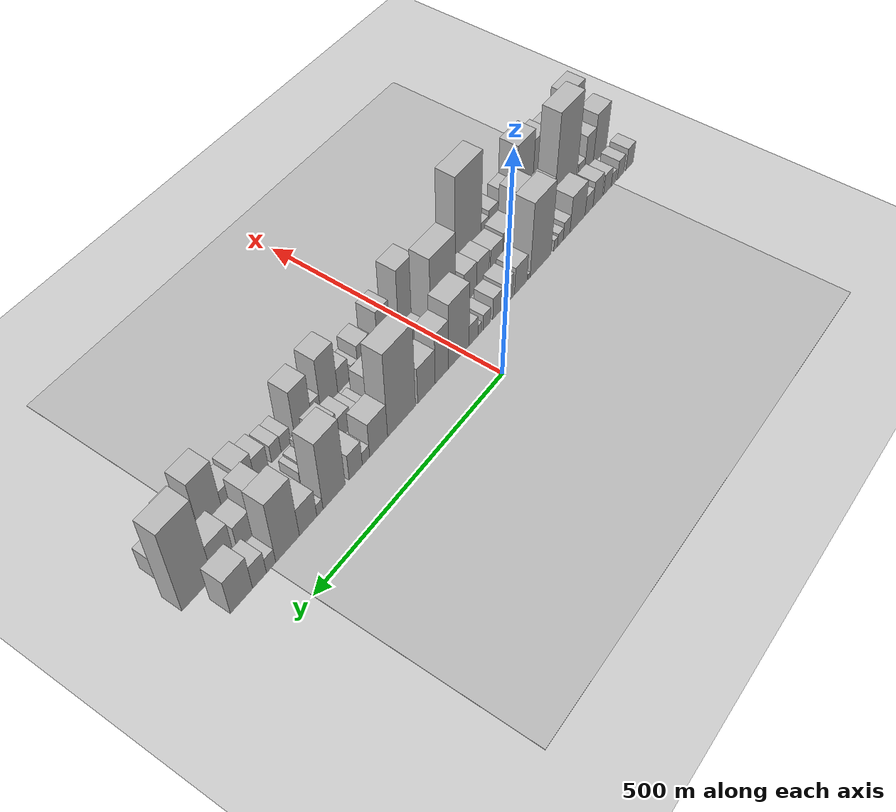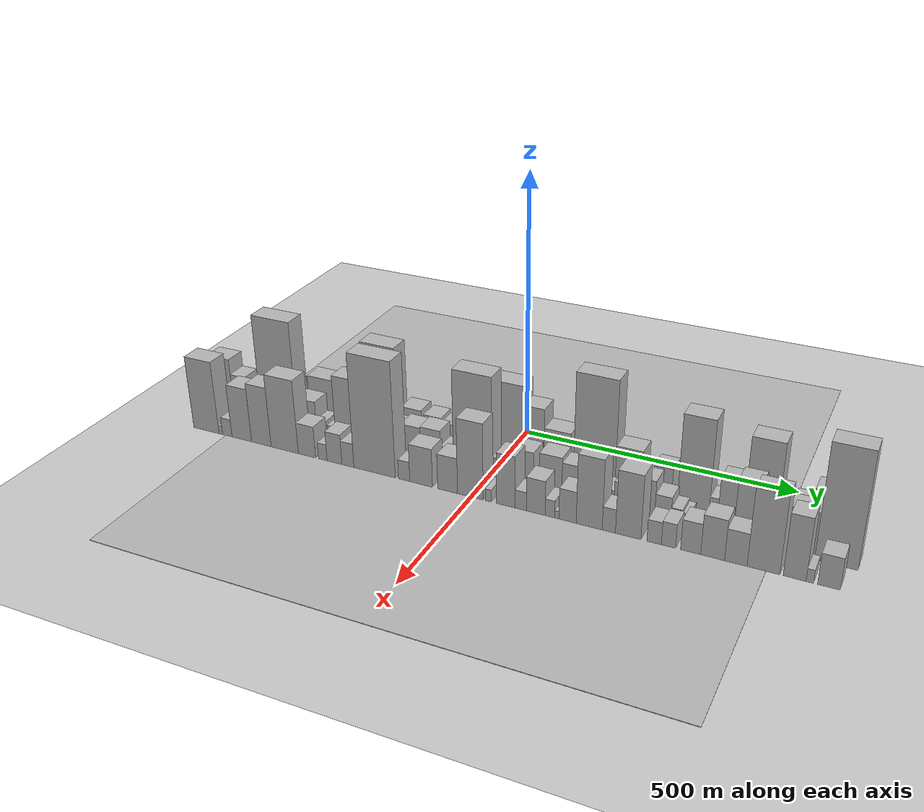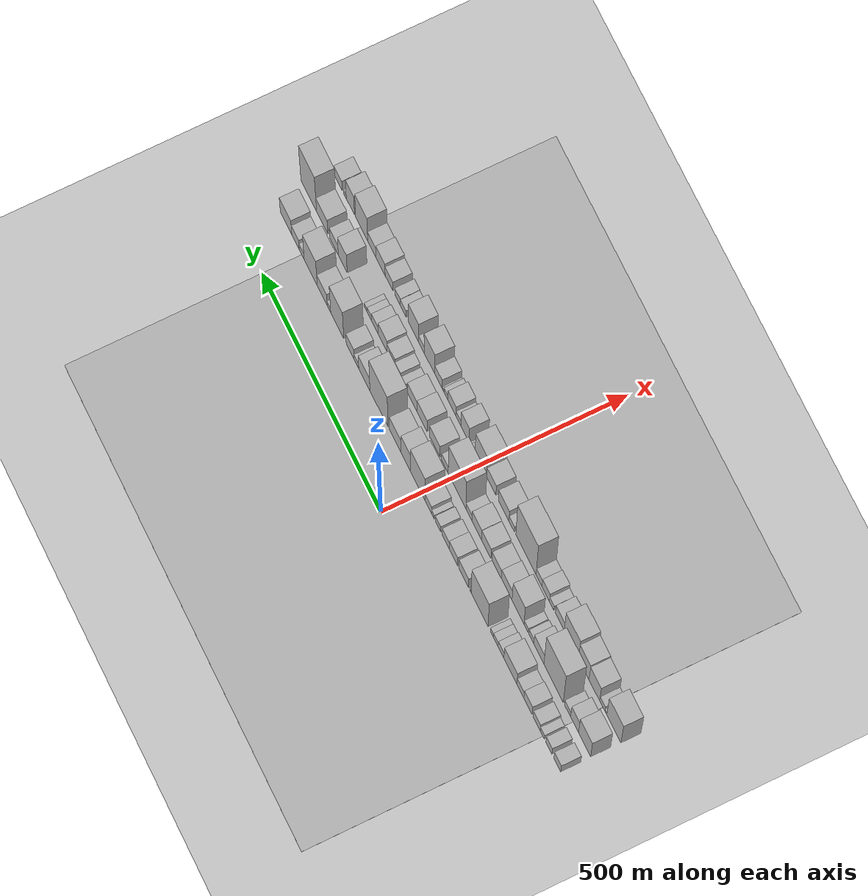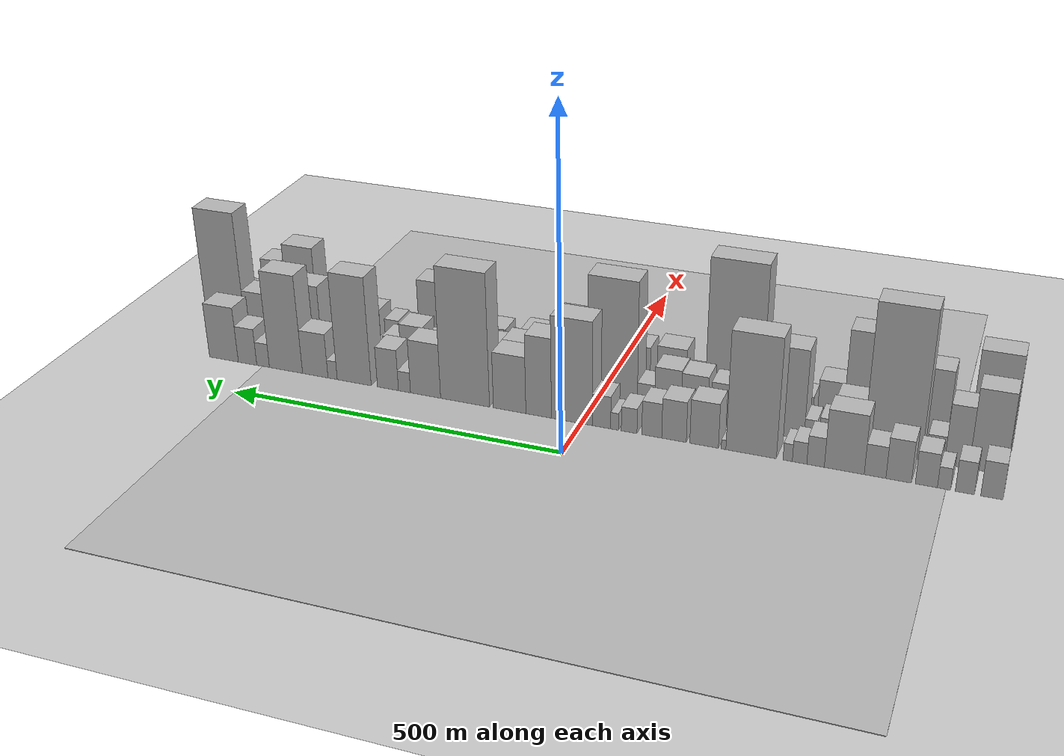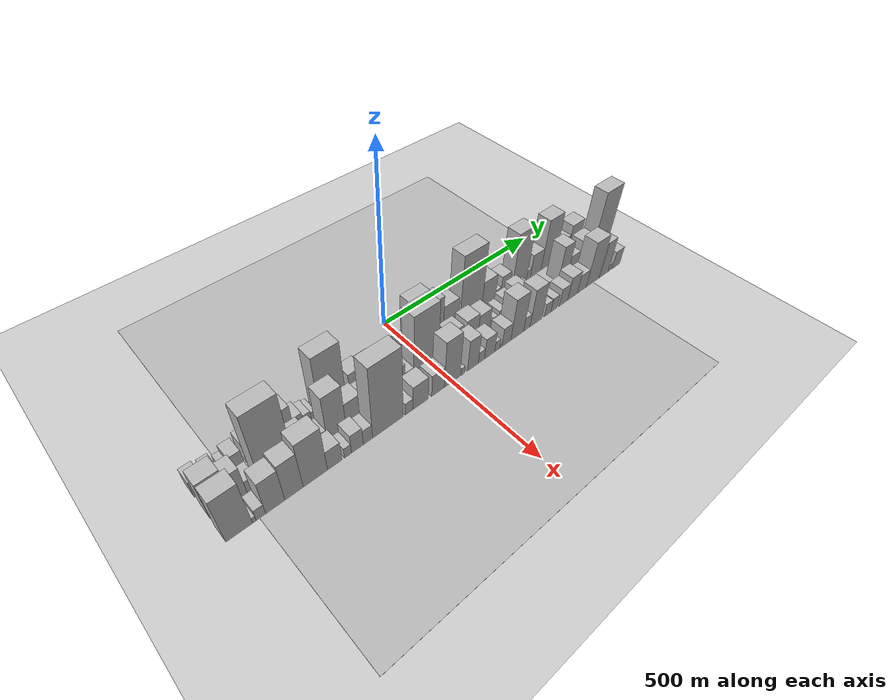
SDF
<?xml version="1.0" encoding="utf-8"?>

<sdf version="1.6">

   <world name="default">

      <gui fullscreen="0">

         <camera name="user_camera">

            <pose>-15 0 4.57585 0 0 0</pose>

            <view_controller>orbit</view_controller>

         </camera>

      </gui>

      <scene>

         <sky>

           <clouds>

             <speed>12</speed>

           </clouds>

         </sky>

         <ambient>0.4 0.4 0.4 1</ambient>

         <background>0.7 0.7 0.7 1</background>

         <shadows>1</shadows>

      </scene>

      <gravity>0 0 -9.8066</gravity>

      <magnetic_field>6e-06 2.3e-05 -4.2e-05</magnetic_field>

      <physics default="0" name="default_physics" type="ode">

         <ode>

            <solver>

               <type>quick</type>

               <iters>10</iters>

               <sor>1.0</sor>

               <use_dynamic_moi_rescaling>0</use_dynamic_moi_rescaling>

            </solver>

            <constraints>

               <cfm>0</cfm>

               <erp>0.2</erp>

               <contact_max_correcting_vel>100</contact_max_correcting_vel>

               <contact_surface_layer>0.001</contact_surface_layer>

            </constraints>

         </ode>

         <max_step_size>0.004</max_step_size>

         <real_time_factor>1</real_time_factor>

         <real_time_update_rate>250</real_time_update_rate>

      </physics>

      <light name="sun" type="directional">

         <cast_shadows>1</cast_shadows>

         <pose>0 0 10 0 0 0</pose>

         <diffuse>0.8 0.8 0.8 1</diffuse>

         <specular>0.2 0.2 0.2 1</specular>

         <attenuation>

            <range>1000</range>

            <constant>0.9</constant>

            <linear>0.01</linear>

            <quadratic>0.001</quadratic>

         </attenuation>

         <direction>-0.5 0.1 -0.9</direction>

      </light>

      <include>

         <name>ground_plane_1</name>

         <uri>model://HANNAS_ground_plane</uri>

         <pose>0 0 0  0 0 0</pose>

      </include>

      <include>

         <name>ground_plane_2</name>

         <uri>model://HANNAS_ground_plane</uri>

         <pose>100 0 0  0 0 0</pose>

      </include>

      <model name="building_1">

         <static>1</static>

         <pose frame="">100.0000 -558.0019 0 0.000000 0.000000 0.000000</pose>

         <link name="link">

            <pose frame="">0 0 27.00 0 0 0</pose>

            <collision name="collision">

               <geometry>

                  <box>

                     <size>40.0000 27.9962 54.0000</size>

                  </box>

               </geometry>

               <max_contacts>10</max_contacts>

               <surface>

                  <contact>

                     <ode/>

                  </contact>

                  <bounce/>

                  <friction>

                     <torsional>

                        <ode/>

                     </torsional>

                     <ode/>

                  </friction>

               </surface>

            </collision>

            <visual name="visual">

               <cast_shadows>0</cast_shadows>

               <geometry>

                  <box>

                     <size>40.0000 27.9962 54.0000</size>

                  </box>

               </geometry>

               <material>

                  <script>

                     <uri>model://HANNAS_wall/materials/scripts</uri>

                     <uri>model://HANNAS_wall/materials/textures</uri>

                     <name>vrc/HANNAS_wall</name>

                  </script>

               </material>

            </visual>

            <self_collide>0</self_collide>

            <enable_wind>0</enable_wind>

            <kinematic>0</kinematic>

         </link>

      </model>

      <model name="building_2">

         <static>1</static>

         <pose frame="">100.0000 -523.8608 0 0.000000 0.000000 0.000000</pose>

         <link name="link">

            <pose frame="">0 0 24.00 0 0 0</pose>

            <collision name="collision">

               <geometry>

                  <box>

                     <size>40.0000 24.2860 48.0000</size>

                  </box>

               </geometry>

               <max_contacts>10</max_contacts>

               <surface>

                  <contact>

                     <ode/>

                  </contact>

                  <bounce/>

                  <friction>

                     <torsional>

                        <ode/>

                     </torsional>

                     <ode/>

                  </friction>

               </surface>

            </collision>

            <visual name="visual">

               <cast_shadows>0</cast_shadows>

               <geometry>

                  <box>

                     <size>40.0000 24.2860 48.0000</size>

                  </box>

               </geometry>

               <material>

                  <script>

                     <uri>model://HANNAS_wall/materials/scripts</uri>

                     <uri>model://HANNAS_wall/materials/textures</uri>

                     <name>vrc/HANNAS_wall</name>

                  </script>

               </material>

            </visual>

            <self_collide>0</self_collide>

            <enable_wind>0</enable_wind>

            <kinematic>0</kinematic>

         </link>

      </model>

      <model name="building_3">

         <static>1</static>

         <pose frame="">100.0000 -497.3234 0 0.000000 0.000000 0.000000</pose>

         <link name="link">

            <pose frame="">0 0 16.50 0 0 0</pose>

            <collision name="collision">

               <geometry>

                  <box>

                     <size>40.0000 16.7890 33.0000</size>

                  </box>

               </geometry>

               <max_contacts>10</max_contacts>

               <surface>

                  <contact>

                     <ode/>

                  </contact>

                  <bounce/>

                  <friction>

                     <torsional>

                        <ode/>

                     </torsional>

                     <ode/>

                  </friction>

               </surface>

            </collision>

            <visual name="visual">

               <cast_shadows>0</cast_shadows>

               <geometry>

                  <box>

                     <size>40.0000 16.7890 33.0000</size>

                  </box>

               </geometry>

               <material>

                  <script>

                     <uri>model://HANNAS_wall/materials/scripts</uri>

                     <uri>model://HANNAS_wall/materials/textures</uri>

                     <name>vrc/HANNAS_wall</name>

                  </script>

               </material>

            </visual>

            <self_collide>0</self_collide>

            <enable_wind>0</enable_wind>

            <kinematic>0</kinematic>

         </link>

      </model>

      <model name="building_4">

         <static>1</static>

         <pose frame="">100.0000 -474.6783 0 0.000000 0.000000 0.000000</pose>

         <link name="link">

            <pose frame="">0 0 25.50 0 0 0</pose>

            <collision name="collision">

               <geometry>

                  <box>

                     <size>40.0000 28.5010 51.0000</size>

                  </box>

               </geometry>

               <max_contacts>10</max_contacts>

               <surface>

                  <contact>

                     <ode/>

                  </contact>

                  <bounce/>

                  <friction>

                     <torsional>

                        <ode/>

                     </torsional>

                     <ode/>

                  </friction>

               </surface>

            </collision>

            <visual name="visual">

               <cast_shadows>0</cast_shadows>

               <geometry>

                  <box>

                     <size>40.0000 28.5010 51.0000</size>

                  </box>

               </geometry>

               <material>

                  <script>

                     <uri>model://HANNAS_wall/materials/scripts</uri>

                     <uri>model://HANNAS_wall/materials/textures</uri>

                     <name>vrc/HANNAS_wall</name>

                  </script>

               </material>

            </visual>

            <self_collide>0</self_collide>

            <enable_wind>0</enable_wind>

            <kinematic>0</kinematic>

         </link>

      </model>

      <model name="building_5">

         <static>1</static>

         <pose frame="">100.0000 -438.8841 0 0.000000 0.000000 0.000000</pose>

         <link name="link">

            <pose frame="">0 0 31.50 0 0 0</pose>

            <collision name="collision">

               <geometry>

                  <box>

                     <size>40.0000 33.0875 63.0000</size>

                  </box>

               </geometry>

               <max_contacts>10</max_contacts>

               <surface>

                  <contact>

                     <ode/>

                  </contact>

                  <bounce/>

                  <friction>

                     <torsional>

                        <ode/>

                     </torsional>

                     <ode/>

                  </friction>

               </surface>

            </collision>

            <visual name="visual">

               <cast_shadows>0</cast_shadows>

               <geometry>

                  <box>

                     <size>40.0000 33.0875 63.0000</size>

                  </box>

               </geometry>

               <material>

                  <script>

                     <uri>model://HANNAS_wall/materials/scripts</uri>

                     <uri>model://HANNAS_wall/materials/textures</uri>

                     <name>vrc/HANNAS_wall</name>

                  </script>

               </material>

            </visual>

            <self_collide>0</self_collide>

            <enable_wind>0</enable_wind>

            <kinematic>0</kinematic>

         </link>

      </model>

      <model name="building_6">

         <static>1</static>

         <pose frame="">100.0000 -408.1292 0 0.000000 0.000000 0.000000</pose>

         <link name="link">

            <pose frame="">0 0 24.00 0 0 0</pose>

            <collision name="collision">

               <geometry>

                  <box>

                     <size>40.0000 28.4222 48.0000</size>

                  </box>

               </geometry>

               <max_contacts>10</max_contacts>

               <surface>

                  <contact>

                     <ode/>

                  </contact>

                  <bounce/>

                  <friction>

                     <torsional>

                        <ode/>

                     </torsional>

                     <ode/>

                  </friction>

               </surface>

            </collision>

            <visual name="visual">

               <cast_shadows>0</cast_shadows>

               <geometry>

                  <box>

                     <size>40.0000 28.4222 48.0000</size>

                  </box>

               </geometry>

               <material>

                  <script>

                     <uri>model://HANNAS_wall/materials/scripts</uri>

                     <uri>model://HANNAS_wall/materials/textures</uri>

                     <name>vrc/HANNAS_wall</name>

                  </script>

               </material>

            </visual>

            <self_collide>0</self_collide>

            <enable_wind>0</enable_wind>

            <kinematic>0</kinematic>

         </link>

      </model>

      <model name="building_7">

         <static>1</static>

         <pose frame="">100.0000 -367.4605 0 0.000000 0.000000 0.000000</pose>

         <link name="link">

            <pose frame="">0 0 45.00 0 0 0</pose>

            <collision name="collision">

               <geometry>

                  <box>

                     <size>40.0000 52.9153 90.0000</size>

                  </box>

               </geometry>

               <max_contacts>10</max_contacts>

               <surface>

                  <contact>

                     <ode/>

                  </contact>

                  <bounce/>

                  <friction>

                     <torsional>

                        <ode/>

                     </torsional>

                     <ode/>

                  </friction>

               </surface>

            </collision>

            <visual name="visual">

               <cast_shadows>0</cast_shadows>

               <geometry>

                  <box>

                     <size>40.0000 52.9153 90.0000</size>

                  </box>

               </geometry>

               <material>

                  <script>

                     <uri>model://HANNAS_wall/materials/scripts</uri>

                     <uri>model://HANNAS_wall/materials/textures</uri>

                     <name>vrc/HANNAS_wall</name>

                  </script>

               </material>

            </visual>

            <self_collide>0</self_collide>

            <enable_wind>0</enable_wind>

            <kinematic>0</kinematic>

         </link>

      </model>

      <model name="building_8">

         <static>1</static>

         <pose frame="">100.0000 -329.2412 0 0.000000 0.000000 0.000000</pose>

         <link name="link">

            <pose frame="">0 0 22.50 0 0 0</pose>

            <collision name="collision">

               <geometry>

                  <box>

                     <size>40.0000 23.5232 45.0000</size>

                  </box>

               </geometry>

               <max_contacts>10</max_contacts>

               <surface>

                  <contact>

                     <ode/>

                  </contact>

                  <bounce/>

                  <friction>

                     <torsional>

                        <ode/>

                     </torsional>

                     <ode/>

                  </friction>

               </surface>

            </collision>

            <visual name="visual">

               <cast_shadows>0</cast_shadows>

               <geometry>

                  <box>

                     <size>40.0000 23.5232 45.0000</size>

                  </box>

               </geometry>

               <material>

                  <script>

                     <uri>model://HANNAS_wall/materials/scripts</uri>

                     <uri>model://HANNAS_wall/materials/textures</uri>

                     <name>vrc/HANNAS_wall</name>

                  </script>

               </material>

            </visual>

            <self_collide>0</self_collide>

            <enable_wind>0</enable_wind>

            <kinematic>0</kinematic>

         </link>

      </model>

      <model name="building_9">

         <static>1</static>

         <pose frame="">100.0000 -307.7043 0 0.000000 0.000000 0.000000</pose>

         <link name="link">

            <pose frame="">0 0 16.50 0 0 0</pose>

            <collision name="collision">

               <geometry>

                  <box>

                     <size>40.0000 19.5506 33.0000</size>

                  </box>

               </geometry>

               <max_contacts>10</max_contacts>

               <surface>

                  <contact>

                     <ode/>

                  </contact>

                  <bounce/>

                  <friction>

                     <torsional>

                        <ode/>

                     </torsional>

                     <ode/>

                  </friction>

               </surface>

            </collision>

            <visual name="visual">

               <cast_shadows>0</cast_shadows>

               <geometry>

                  <box>

                     <size>40.0000 19.5506 33.0000</size>

                  </box>

               </geometry>

               <material>

                  <script>

                     <uri>model://HANNAS_wall/materials/scripts</uri>

                     <uri>model://HANNAS_wall/materials/textures</uri>

                     <name>vrc/HANNAS_wall</name>

                  </script>

               </material>

            </visual>

            <self_collide>0</self_collide>

            <enable_wind>0</enable_wind>

            <kinematic>0</kinematic>

         </link>

      </model>

      <model name="building_10">

         <static>1</static>

         <pose frame="">100.0000 -291.6246 0 0.000000 0.000000 0.000000</pose>

         <link name="link">

            <pose frame="">0 0 13.50 0 0 0</pose>

            <collision name="collision">

               <geometry>

                  <box>

                     <size>40.0000 12.6088 27.0000</size>

                  </box>

               </geometry>

               <max_contacts>10</max_contacts>

               <surface>

                  <contact>

                     <ode/>

                  </contact>

                  <bounce/>

                  <friction>

                     <torsional>

                        <ode/>

                     </torsional>

                     <ode/>

                  </friction>

               </surface>

            </collision>

            <visual name="visual">

               <cast_shadows>0</cast_shadows>

               <geometry>

                  <box>

                     <size>40.0000 12.6088 27.0000</size>

                  </box>

               </geometry>

               <material>

                  <script>

                     <uri>model://HANNAS_wall/materials/scripts</uri>

                     <uri>model://HANNAS_wall/materials/textures</uri>

                     <name>vrc/HANNAS_wall</name>

                  </script>

               </material>

            </visual>

            <self_collide>0</self_collide>

            <enable_wind>0</enable_wind>

            <kinematic>0</kinematic>

         </link>

      </model>

      <model name="building_11">

         <static>1</static>

         <pose frame="">100.0000 -241.5923 0 0.000000 0.000000 0.000000</pose>

         <link name="link">

            <pose frame="">0 0 91.50 0 0 0</pose>

            <collision name="collision">

               <geometry>

                  <box>

                     <size>40.0000 69.4558 183.0000</size>

                  </box>

               </geometry>

               <max_contacts>10</max_contacts>

               <surface>

                  <contact>

                     <ode/>

                  </contact>

                  <bounce/>

                  <friction>

                     <torsional>

                        <ode/>

                     </torsional>

                     <ode/>

                  </friction>

               </surface>

            </collision>

            <visual name="visual">

               <cast_shadows>0</cast_shadows>

               <geometry>

                  <box>

                     <size>40.0000 69.4558 183.0000</size>

                  </box>

               </geometry>

               <material>

                  <script>

                     <uri>model://HANNAS_wall/materials/scripts</uri>

                     <uri>model://HANNAS_wall/materials/textures</uri>

                     <name>vrc/HANNAS_wall</name>

                  </script>

               </material>

            </visual>

            <self_collide>0</self_collide>

            <enable_wind>0</enable_wind>

            <kinematic>0</kinematic>

         </link>

      </model>

      <model name="building_12">

         <static>1</static>

         <pose frame="">100.0000 -203.6578 0 0.000000 0.000000 0.000000</pose>

         <link name="link">

            <pose frame="">0 0 7.50 0 0 0</pose>

            <collision name="collision">

               <geometry>

                  <box>

                     <size>40.0000 6.4133 15.0000</size>

                  </box>

               </geometry>

               <max_contacts>10</max_contacts>

               <surface>

                  <contact>

                     <ode/>

                  </contact>

                  <bounce/>

                  <friction>

                     <torsional>

                        <ode/>

                     </torsional>

                     <ode/>

                  </friction>

               </surface>

            </collision>

            <visual name="visual">

               <cast_shadows>0</cast_shadows>

               <geometry>

                  <box>

                     <size>40.0000 6.4133 15.0000</size>

                  </box>

               </geometry>

               <material>

                  <script>

                     <uri>model://HANNAS_wall/materials/scripts</uri>

                     <uri>model://HANNAS_wall/materials/textures</uri>

                     <name>vrc/HANNAS_wall</name>

                  </script>

               </material>

            </visual>

            <self_collide>0</self_collide>

            <enable_wind>0</enable_wind>

            <kinematic>0</kinematic>

         </link>

      </model>

      <model name="building_13">

         <static>1</static>

         <pose frame="">100.0000 -176.4367 0 0.000000 0.000000 0.000000</pose>

         <link name="link">

            <pose frame="">0 0 34.50 0 0 0</pose>

            <collision name="collision">

               <geometry>

                  <box>

                     <size>40.0000 40.0288 69.0000</size>

                  </box>

               </geometry>

               <max_contacts>10</max_contacts>

               <surface>

                  <contact>

                     <ode/>

                  </contact>

                  <bounce/>

                  <friction>

                     <torsional>

                        <ode/>

                     </torsional>

                     <ode/>

                  </friction>

               </surface>

            </collision>

            <visual name="visual">

               <cast_shadows>0</cast_shadows>

               <geometry>

                  <box>

                     <size>40.0000 40.0288 69.0000</size>

                  </box>

               </geometry>

               <material>

                  <script>

                     <uri>model://HANNAS_wall/materials/scripts</uri>

                     <uri>model://HANNAS_wall/materials/textures</uri>

                     <name>vrc/HANNAS_wall</name>

                  </script>

               </material>

            </visual>

            <self_collide>0</self_collide>

            <enable_wind>0</enable_wind>

            <kinematic>0</kinematic>

         </link>

      </model>

      <model name="building_14">

         <static>1</static>

         <pose frame="">100.0000 -134.0213 0 0.000000 0.000000 0.000000</pose>

         <link name="link">

            <pose frame="">0 0 31.50 0 0 0</pose>

            <collision name="collision">

               <geometry>

                  <box>

                     <size>40.0000 34.8020 63.0000</size>

                  </box>

               </geometry>

               <max_contacts>10</max_contacts>

               <surface>

                  <contact>

                     <ode/>

                  </contact>

                  <bounce/>

                  <friction>

                     <torsional>

                        <ode/>

                     </torsional>

                     <ode/>

                  </friction>

               </surface>

            </collision>

            <visual name="visual">

               <cast_shadows>0</cast_shadows>

               <geometry>

                  <box>

                     <size>40.0000 34.8020 63.0000</size>

                  </box>

               </geometry>

               <material>

                  <script>

                     <uri>model://HANNAS_wall/materials/scripts</uri>

                     <uri>model://HANNAS_wall/materials/textures</uri>

                     <name>vrc/HANNAS_wall</name>

                  </script>

               </material>

            </visual>

            <self_collide>0</self_collide>

            <enable_wind>0</enable_wind>

            <kinematic>0</kinematic>

         </link>

      </model>

      <model name="building_15">

         <static>1</static>

         <pose frame="">100.0000 -102.4216 0 0.000000 0.000000 0.000000</pose>

         <link name="link">

            <pose frame="">0 0 27.00 0 0 0</pose>

            <collision name="collision">

               <geometry>

                  <box>

                     <size>40.0000 28.3974 54.0000</size>

                  </box>

               </geometry>

               <max_contacts>10</max_contacts>

               <surface>

                  <contact>

                     <ode/>

                  </contact>

                  <bounce/>

                  <friction>

                     <torsional>

                        <ode/>

                     </torsional>

                     <ode/>

                  </friction>

               </surface>

            </collision>

            <visual name="visual">

               <cast_shadows>0</cast_shadows>

               <geometry>

                  <box>

                     <size>40.0000 28.3974 54.0000</size>

                  </box>

               </geometry>

               <material>

                  <script>

                     <uri>model://HANNAS_wall/materials/scripts</uri>

                     <uri>model://HANNAS_wall/materials/textures</uri>

                     <name>vrc/HANNAS_wall</name>

                  </script>

               </material>

            </visual>

            <self_collide>0</self_collide>

            <enable_wind>0</enable_wind>

            <kinematic>0</kinematic>

         </link>

      </model>

      <model name="building_16">

         <static>1</static>

         <pose frame="">100.0000 -69.9019 0 0.000000 0.000000 0.000000</pose>

         <link name="link">

            <pose frame="">0 0 19.50 0 0 0</pose>

            <collision name="collision">

               <geometry>

                  <box>

                     <size>40.0000 22.6419 39.0000</size>

                  </box>

               </geometry>

               <max_contacts>10</max_contacts>

               <surface>

                  <contact>

                     <ode/>

                  </contact>

                  <bounce/>

                  <friction>

                     <torsional>

                        <ode/>

                     </torsional>

                     <ode/>

                  </friction>

               </surface>

            </collision>

            <visual name="visual">

               <cast_shadows>0</cast_shadows>

               <geometry>

                  <box>

                     <size>40.0000 22.6419 39.0000</size>

                  </box>

               </geometry>

               <material>

                  <script>

                     <uri>model://HANNAS_wall/materials/scripts</uri>

                     <uri>model://HANNAS_wall/materials/textures</uri>

                     <name>vrc/HANNAS_wall</name>

                  </script>

               </material>

            </visual>

            <self_collide>0</self_collide>

            <enable_wind>0</enable_wind>

            <kinematic>0</kinematic>

         </link>

      </model>

      <model name="building_17">

         <static>1</static>

         <pose frame="">100.0000 -48.9217 0 0.000000 0.000000 0.000000</pose>

         <link name="link">

            <pose frame="">0 0 13.50 0 0 0</pose>

            <collision name="collision">

               <geometry>

                  <box>

                     <size>40.0000 11.3185 27.0000</size>

                  </box>

               </geometry>

               <max_contacts>10</max_contacts>

               <surface>

                  <contact>

                     <ode/>

                  </contact>

                  <bounce/>

                  <friction>

                     <torsional>

                        <ode/>

                     </torsional>

                     <ode/>

                  </friction>

               </surface>

            </collision>

            <visual name="visual">

               <cast_shadows>0</cast_shadows>

               <geometry>

                  <box>

                     <size>40.0000 11.3185 27.0000</size>

                  </box>

               </geometry>

               <material>

                  <script>

                     <uri>model://HANNAS_wall/materials/scripts</uri>

                     <uri>model://HANNAS_wall/materials/textures</uri>

                     <name>vrc/HANNAS_wall</name>

                  </script>

               </material>

            </visual>

            <self_collide>0</self_collide>

            <enable_wind>0</enable_wind>

            <kinematic>0</kinematic>

         </link>

      </model>

      <model name="building_18">

         <static>1</static>

         <pose frame="">100.0000 -29.7949 0 0.000000 0.000000 0.000000</pose>

         <link name="link">

            <pose frame="">0 0 25.50 0 0 0</pose>

            <collision name="collision">

               <geometry>

                  <box>

                     <size>40.0000 26.9351 51.0000</size>

                  </box>

               </geometry>

               <max_contacts>10</max_contacts>

               <surface>

                  <contact>

                     <ode/>

                  </contact>

                  <bounce/>

                  <friction>

                     <torsional>

                        <ode/>

                     </torsional>

                     <ode/>

                  </friction>

               </surface>

            </collision>

            <visual name="visual">

               <cast_shadows>0</cast_shadows>

               <geometry>

                  <box>

                     <size>40.0000 26.9351 51.0000</size>

                  </box>

               </geometry>

               <material>

                  <script>

                     <uri>model://HANNAS_wall/materials/scripts</uri>

                     <uri>model://HANNAS_wall/materials/textures</uri>

                     <name>vrc/HANNAS_wall</name>

                  </script>

               </material>

            </visual>

            <self_collide>0</self_collide>

            <enable_wind>0</enable_wind>

            <kinematic>0</kinematic>

         </link>

      </model>

      <model name="building_19">

         <static>1</static>

         <pose frame="">100.0000 13.7449 0 0.000000 0.000000 0.000000</pose>

         <link name="link">

            <pose frame="">0 0 81.00 0 0 0</pose>

            <collision name="collision">

               <geometry>

                  <box>

                     <size>40.0000 60.1446 162.0000</size>

                  </box>

               </geometry>

               <max_contacts>10</max_contacts>

               <surface>

                  <contact>

                     <ode/>

                  </contact>

                  <bounce/>

                  <friction>

                     <torsional>

                        <ode/>

                     </torsional>

                     <ode/>

                  </friction>

               </surface>

            </collision>

            <visual name="visual">

               <cast_shadows>0</cast_shadows>

               <geometry>

                  <box>

                     <size>40.0000 60.1446 162.0000</size>

                  </box>

               </geometry>

               <material>

                  <script>

                     <uri>model://HANNAS_wall/materials/scripts</uri>

                     <uri>model://HANNAS_wall/materials/textures</uri>

                     <name>vrc/HANNAS_wall</name>

                  </script>

               </material>

            </visual>

            <self_collide>0</self_collide>

            <enable_wind>0</enable_wind>

            <kinematic>0</kinematic>

         </link>

      </model>

      <model name="building_20">

         <static>1</static>

         <pose frame="">100.0000 62.9735 0 0.000000 0.000000 0.000000</pose>

         <link name="link">

            <pose frame="">0 0 63.00 0 0 0</pose>

            <collision name="collision">

               <geometry>

                  <box>

                     <size>40.0000 38.3127 126.0000</size>

                  </box>

               </geometry>

               <max_contacts>10</max_contacts>

               <surface>

                  <contact>

                     <ode/>

                  </contact>

                  <bounce/>

                  <friction>

                     <torsional>

                        <ode/>

                     </torsional>

                     <ode/>

                  </friction>

               </surface>

            </collision>

            <visual name="visual">

               <cast_shadows>0</cast_shadows>

               <geometry>

                  <box>

                     <size>40.0000 38.3127 126.0000</size>

                  </box>

               </geometry>

               <material>

                  <script>

                     <uri>model://HANNAS_wall/materials/scripts</uri>

                     <uri>model://HANNAS_wall/materials/textures</uri>

                     <name>vrc/HANNAS_wall</name>

                  </script>

               </material>

            </visual>

            <self_collide>0</self_collide>

            <enable_wind>0</enable_wind>

            <kinematic>0</kinematic>

         </link>

      </model>

      <model name="building_21">

         <static>1</static>

         <pose frame="">100.0000 106.6923 0 0.000000 0.000000 0.000000</pose>

         <link name="link">

            <pose frame="">0 0 45.00 0 0 0</pose>

            <collision name="collision">

               <geometry>

                  <box>

                     <size>40.0000 49.1248 90.0000</size>

                  </box>

               </geometry>

               <max_contacts>10</max_contacts>

               <surface>

                  <contact>

                     <ode/>

                  </contact>

                  <bounce/>

                  <friction>

                     <torsional>

                        <ode/>

                     </torsional>

                     <ode/>

                  </friction>

               </surface>

            </collision>

            <visual name="visual">

               <cast_shadows>0</cast_shadows>

               <geometry>

                  <box>

                     <size>40.0000 49.1248 90.0000</size>

                  </box>

               </geometry>

               <material>

                  <script>

                     <uri>model://HANNAS_wall/materials/scripts</uri>

                     <uri>model://HANNAS_wall/materials/textures</uri>

                     <name>vrc/HANNAS_wall</name>

                  </script>

               </material>

            </visual>

            <self_collide>0</self_collide>

            <enable_wind>0</enable_wind>

            <kinematic>0</kinematic>

         </link>

      </model>

      <model name="building_22">

         <static>1</static>

         <pose frame="">100.0000 174.9727 0 0.000000 0.000000 0.000000</pose>

         <link name="link">

            <pose frame="">0 0 105.00 0 0 0</pose>

            <collision name="collision">

               <geometry>

                  <box>

                     <size>40.0000 75.4360 210.0000</size>

                  </box>

               </geometry>

               <max_contacts>10</max_contacts>

               <surface>

                  <contact>

                     <ode/>

                  </contact>

                  <bounce/>

                  <friction>

                     <torsional>

                        <ode/>

                     </torsional>

                     <ode/>

                  </friction>

               </surface>

            </collision>

            <visual name="visual">

               <cast_shadows>0</cast_shadows>

               <geometry>

                  <box>

                     <size>40.0000 75.4360 210.0000</size>

                  </box>

               </geometry>

               <material>

                  <script>

                     <uri>model://HANNAS_wall/materials/scripts</uri>

                     <uri>model://HANNAS_wall/materials/textures</uri>

                     <name>vrc/HANNAS_wall</name>

                  </script>

               </material>

            </visual>

            <self_collide>0</self_collide>

            <enable_wind>0</enable_wind>

            <kinematic>0</kinematic>

         </link>

      </model>

      <model name="building_23">

         <static>1</static>

         <pose frame="">100.0000 236.2679 0 0.000000 0.000000 0.000000</pose>

         <link name="link">

            <pose frame="">0 0 43.50 0 0 0</pose>

            <collision name="collision">

               <geometry>

                  <box>

                     <size>40.0000 47.1543 87.0000</size>

                  </box>

               </geometry>

               <max_contacts>10</max_contacts>

               <surface>

                  <contact>

                     <ode/>

                  </contact>

                  <bounce/>

                  <friction>

                     <torsional>

                        <ode/>

                     </torsional>

                     <ode/>

                  </friction>

               </surface>

            </collision>

            <visual name="visual">

               <cast_shadows>0</cast_shadows>

               <geometry>

                  <box>

                     <size>40.0000 47.1543 87.0000</size>

                  </box>

               </geometry>

               <material>

                  <script>

                     <uri>model://HANNAS_wall/materials/scripts</uri>

                     <uri>model://HANNAS_wall/materials/textures</uri>

                     <name>vrc/HANNAS_wall</name>

                  </script>

               </material>

            </visual>

            <self_collide>0</self_collide>

            <enable_wind>0</enable_wind>

            <kinematic>0</kinematic>

         </link>

      </model>

      <model name="building_24">

         <static>1</static>

         <pose frame="">100.0000 269.3760 0 0.000000 0.000000 0.000000</pose>

         <link name="link">

            <pose frame="">0 0 16.50 0 0 0</pose>

            <collision name="collision">

               <geometry>

                  <box>

                     <size>40.0000 19.0619 33.0000</size>

                  </box>

               </geometry>

               <max_contacts>10</max_contacts>

               <surface>

                  <contact>

                     <ode/>

                  </contact>

                  <bounce/>

                  <friction>

                     <torsional>

                        <ode/>

                     </torsional>

                     <ode/>

                  </friction>

               </surface>

            </collision>

            <visual name="visual">

               <cast_shadows>0</cast_shadows>

               <geometry>

                  <box>

                     <size>40.0000 19.0619 33.0000</size>

                  </box>

               </geometry>

               <material>

                  <script>

                     <uri>model://HANNAS_wall/materials/scripts</uri>

                     <uri>model://HANNAS_wall/materials/textures</uri>

                     <name>vrc/HANNAS_wall</name>

                  </script>

               </material>

            </visual>

            <self_collide>0</self_collide>

            <enable_wind>0</enable_wind>

            <kinematic>0</kinematic>

         </link>

      </model>

      <model name="building_25">

         <static>1</static>

         <pose frame="">100.0000 295.6303 0 0.000000 0.000000 0.000000</pose>

         <link name="link">

            <pose frame="">0 0 33.00 0 0 0</pose>

            <collision name="collision">

               <geometry>

                  <box>

                     <size>40.0000 33.4467 66.0000</size>

                  </box>

               </geometry>

               <max_contacts>10</max_contacts>

               <surface>

                  <contact>

                     <ode/>

                  </contact>

                  <bounce/>

                  <friction>

                     <torsional>

                        <ode/>

                     </torsional>

                     <ode/>

                  </friction>

               </surface>

            </collision>

            <visual name="visual">

               <cast_shadows>0</cast_shadows>

               <geometry>

                  <box>

                     <size>40.0000 33.4467 66.0000</size>

                  </box>

               </geometry>

               <material>

                  <script>

                     <uri>model://HANNAS_wall/materials/scripts</uri>

                     <uri>model://HANNAS_wall/materials/textures</uri>

                     <name>vrc/HANNAS_wall</name>

                  </script>

               </material>

            </visual>

            <self_collide>0</self_collide>

            <enable_wind>0</enable_wind>

            <kinematic>0</kinematic>

         </link>

      </model>

      <model name="building_26">

         <static>1</static>

         <pose frame="">100.0000 349.8147 0 0.000000 0.000000 0.000000</pose>

         <link name="link">

            <pose frame="">0 0 87.00 0 0 0</pose>

            <collision name="collision">

               <geometry>

                  <box>

                     <size>40.0000 54.9222 174.0000</size>

                  </box>

               </geometry>

               <max_contacts>10</max_contacts>

               <surface>

                  <contact>

                     <ode/>

                  </contact>

                  <bounce/>

                  <friction>

                     <torsional>

                        <ode/>

                     </torsional>

                     <ode/>

                  </friction>

               </surface>

            </collision>

            <visual name="visual">

               <cast_shadows>0</cast_shadows>

               <geometry>

                  <box>

                     <size>40.0000 54.9222 174.0000</size>

                  </box>

               </geometry>

               <material>

                  <script>

                     <uri>model://HANNAS_wall/materials/scripts</uri>

                     <uri>model://HANNAS_wall/materials/textures</uri>

                     <name>vrc/HANNAS_wall</name>

                  </script>

               </material>

            </visual>

            <self_collide>0</self_collide>

            <enable_wind>0</enable_wind>

            <kinematic>0</kinematic>

         </link>

      </model>

      <model name="building_27">

         <static>1</static>

         <pose frame="">100.0000 384.7906 0 0.000000 0.000000 0.000000</pose>

         <link name="link">

            <pose frame="">0 0 15.00 0 0 0</pose>

            <collision name="collision">

               <geometry>

                  <box>

                     <size>40.0000 15.0295 30.0000</size>

                  </box>

               </geometry>

               <max_contacts>10</max_contacts>

               <surface>

                  <contact>

                     <ode/>

                  </contact>

                  <bounce/>

                  <friction>

                     <torsional>

                        <ode/>

                     </torsional>

                     <ode/>

                  </friction>

               </surface>

            </collision>

            <visual name="visual">

               <cast_shadows>0</cast_shadows>

               <geometry>

                  <box>

                     <size>40.0000 15.0295 30.0000</size>

                  </box>

               </geometry>

               <material>

                  <script>

                     <uri>model://HANNAS_wall/materials/scripts</uri>

                     <uri>model://HANNAS_wall/materials/textures</uri>

                     <name>vrc/HANNAS_wall</name>

                  </script>

               </material>

            </visual>

            <self_collide>0</self_collide>

            <enable_wind>0</enable_wind>

            <kinematic>0</kinematic>

         </link>

      </model>

      <model name="building_28">

         <static>1</static>

         <pose frame="">100.0000 413.1825 0 0.000000 0.000000 0.000000</pose>

         <link name="link">

            <pose frame="">0 0 36.00 0 0 0</pose>

            <collision name="collision">

               <geometry>

                  <box>

                     <size>40.0000 41.7544 72.0000</size>

                  </box>

               </geometry>

               <max_contacts>10</max_contacts>

               <surface>

                  <contact>

                     <ode/>

                  </contact>

                  <bounce/>

                  <friction>

                     <torsional>

                        <ode/>

                     </torsional>

                     <ode/>

                  </friction>

               </surface>

            </collision>

            <visual name="visual">

               <cast_shadows>0</cast_shadows>

               <geometry>

                  <box>

                     <size>40.0000 41.7544 72.0000</size>

                  </box>

               </geometry>

               <material>

                  <script>

                     <uri>model://HANNAS_wall/materials/scripts</uri>

                     <uri>model://HANNAS_wall/materials/textures</uri>

                     <name>vrc/HANNAS_wall</name>

                  </script>

               </material>

            </visual>

            <self_collide>0</self_collide>

            <enable_wind>0</enable_wind>

            <kinematic>0</kinematic>

         </link>

      </model>

      <model name="building_29">

         <static>1</static>

         <pose frame="">100.0000 461.6059 0 0.000000 0.000000 0.000000</pose>

         <link name="link">

            <pose frame="">0 0 79.50 0 0 0</pose>

            <collision name="collision">

               <geometry>

                  <box>

                     <size>40.0000 55.0923 159.0000</size>

                  </box>

               </geometry>

               <max_contacts>10</max_contacts>

               <surface>

                  <contact>

                     <ode/>

                  </contact>

                  <bounce/>

                  <friction>

                     <torsional>

                        <ode/>

                     </torsional>

                     <ode/>

                  </friction>

               </surface>

            </collision>

            <visual name="visual">

               <cast_shadows>0</cast_shadows>

               <geometry>

                  <box>

                     <size>40.0000 55.0923 159.0000</size>

                  </box>

               </geometry>

               <material>

                  <script>

                     <uri>model://HANNAS_wall/materials/scripts</uri>

                     <uri>model://HANNAS_wall/materials/textures</uri>

                     <name>vrc/HANNAS_wall</name>

                  </script>

               </material>

            </visual>

            <self_collide>0</self_collide>

            <enable_wind>0</enable_wind>

            <kinematic>0</kinematic>

         </link>

      </model>

      <model name="building_30">

         <static>1</static>

         <pose frame="">100.0000 499.7639 0 0.000000 0.000000 0.000000</pose>

         <link name="link">

            <pose frame="">0 0 19.50 0 0 0</pose>

            <collision name="collision">

               <geometry>

                  <box>

                     <size>40.0000 21.2238 39.0000</size>

                  </box>

               </geometry>

               <max_contacts>10</max_contacts>

               <surface>

                  <contact>

                     <ode/>

                  </contact>

                  <bounce/>

                  <friction>

                     <torsional>

                        <ode/>

                     </torsional>

                     <ode/>

                  </friction>

               </surface>

            </collision>

            <visual name="visual">

               <cast_shadows>0</cast_shadows>

               <geometry>

                  <box>

                     <size>40.0000 21.2238 39.0000</size>

                  </box>

               </geometry>

               <material>

                  <script>

                     <uri>model://HANNAS_wall/materials/scripts</uri>

                     <uri>model://HANNAS_wall/materials/textures</uri>

                     <name>vrc/HANNAS_wall</name>

                  </script>

               </material>

            </visual>

            <self_collide>0</self_collide>

            <enable_wind>0</enable_wind>

            <kinematic>0</kinematic>

         </link>

      </model>

      <model name="building_31">

         <static>1</static>

         <pose frame="">100.0000 526.0002 0 0.000000 0.000000 0.000000</pose>

         <link name="link">

            <pose frame="">0 0 30.00 0 0 0</pose>

            <collision name="collision">

               <geometry>

                  <box>

                     <size>40.0000 31.2488 60.0000</size>

                  </box>

               </geometry>

               <max_contacts>10</max_contacts>

               <surface>

                  <contact>

                     <ode/>

                  </contact>

                  <bounce/>

                  <friction>

                     <torsional>

                        <ode/>

                     </torsional>

                     <ode/>

                  </friction>

               </surface>

            </collision>

            <visual name="visual">

               <cast_shadows>0</cast_shadows>

               <geometry>

                  <box>

                     <size>40.0000 31.2488 60.0000</size>

                  </box>

               </geometry>

               <material>

                  <script>

                     <uri>model://HANNAS_wall/materials/scripts</uri>

                     <uri>model://HANNAS_wall/materials/textures</uri>

                     <name>vrc/HANNAS_wall</name>

                  </script>

               </material>

            </visual>

            <self_collide>0</self_collide>

            <enable_wind>0</enable_wind>

            <kinematic>0</kinematic>

         </link>

      </model>

      <model name="building_32">

         <static>1</static>

         <pose frame="">100.0000 566.1386 0 0.000000 0.000000 0.000000</pose>

         <link name="link">

            <pose frame="">0 0 45.00 0 0 0</pose>

            <collision name="collision">

               <geometry>

                  <box>

                     <size>40.0000 49.0280 90.0000</size>

                  </box>

               </geometry>

               <max_contacts>10</max_contacts>

               <surface>

                  <contact>

                     <ode/>

                  </contact>

                  <bounce/>

                  <friction>

                     <torsional>

                        <ode/>

                     </torsional>

                     <ode/>

                  </friction>

               </surface>

            </collision>

            <visual name="visual">

               <cast_shadows>0</cast_shadows>

               <geometry>

                  <box>

                     <size>40.0000 49.0280 90.0000</size>

                  </box>

               </geometry>

               <material>

                  <script>

                     <uri>model://HANNAS_wall/materials/scripts</uri>

                     <uri>model://HANNAS_wall/materials/textures</uri>

                     <name>vrc/HANNAS_wall</name>

                  </script>

               </material>

            </visual>

            <self_collide>0</self_collide>

            <enable_wind>0</enable_wind>

            <kinematic>0</kinematic>

         </link>

      </model>

      <model name="building_33">

         <static>1</static>

         <pose frame="">160.0000 -546.7151 0 0.000000 0.000000 0.000000</pose>

         <link name="link">

            <pose frame="">0 0 61.50 0 0 0</pose>

            <collision name="collision">

               <geometry>

                  <box>

                     <size>40.0000 48.5699 123.0000</size>

                  </box>

               </geometry>

               <max_contacts>10</max_contacts>

               <surface>

                  <contact>

                     <ode/>

                  </contact>

                  <bounce/>

                  <friction>

                     <torsional>

                        <ode/>

                     </torsional>

                     <ode/>

                  </friction>

               </surface>

            </collision>

            <visual name="visual">

               <cast_shadows>0</cast_shadows>

               <geometry>

                  <box>

                     <size>40.0000 48.5699 123.0000</size>

                  </box>

               </geometry>

               <material>

                  <script>

                     <uri>model://HANNAS_wall/materials/scripts</uri>

                     <uri>model://HANNAS_wall/materials/textures</uri>

                     <name>vrc/HANNAS_wall</name>

                  </script>

               </material>

            </visual>

            <self_collide>0</self_collide>

            <enable_wind>0</enable_wind>

            <kinematic>0</kinematic>

         </link>

      </model>

      <model name="building_34">

         <static>1</static>

         <pose frame="">160.0000 -506.3206 0 0.000000 0.000000 0.000000</pose>

         <link name="link">

            <pose frame="">0 0 46.50 0 0 0</pose>

            <collision name="collision">

               <geometry>

                  <box>

                     <size>40.0000 32.2191 93.0000</size>

                  </box>

               </geometry>

               <max_contacts>10</max_contacts>

               <surface>

                  <contact>

                     <ode/>

                  </contact>

                  <bounce/>

                  <friction>

                     <torsional>

                        <ode/>

                     </torsional>

                     <ode/>

                  </friction>

               </surface>

            </collision>

            <visual name="visual">

               <cast_shadows>0</cast_shadows>

               <geometry>

                  <box>

                     <size>40.0000 32.2191 93.0000</size>

                  </box>

               </geometry>

               <material>

                  <script>

                     <uri>model://HANNAS_wall/materials/scripts</uri>

                     <uri>model://HANNAS_wall/materials/textures</uri>

                     <name>vrc/HANNAS_wall</name>

                  </script>

               </material>

            </visual>

            <self_collide>0</self_collide>

            <enable_wind>0</enable_wind>

            <kinematic>0</kinematic>

         </link>

      </model>

      <model name="building_35">

         <static>1</static>

         <pose frame="">160.0000 -477.7896 0 0.000000 0.000000 0.000000</pose>

         <link name="link">

            <pose frame="">0 0 21.00 0 0 0</pose>

            <collision name="collision">

               <geometry>

                  <box>

                     <size>40.0000 24.8428 42.0000</size>

                  </box>

               </geometry>

               <max_contacts>10</max_contacts>

               <surface>

                  <contact>

                     <ode/>

                  </contact>

                  <bounce/>

                  <friction>

                     <torsional>

                        <ode/>

                     </torsional>

                     <ode/>

                  </friction>

               </surface>

            </collision>

            <visual name="visual">

               <cast_shadows>0</cast_shadows>

               <geometry>

                  <box>

                     <size>40.0000 24.8428 42.0000</size>

                  </box>

               </geometry>

               <material>

                  <script>

                     <uri>model://HANNAS_wall/materials/scripts</uri>

                     <uri>model://HANNAS_wall/materials/textures</uri>

                     <name>vrc/HANNAS_wall</name>

                  </script>

               </material>

            </visual>

            <self_collide>0</self_collide>

            <enable_wind>0</enable_wind>

            <kinematic>0</kinematic>

         </link>

      </model>

      <model name="building_36">

         <static>1</static>

         <pose frame="">160.0000 -421.2338 0 0.000000 0.000000 0.000000</pose>

         <link name="link">

            <pose frame="">0 0 112.50 0 0 0</pose>

            <collision name="collision">

               <geometry>

                  <box>

                     <size>40.0000 78.2689 225.0000</size>

                  </box>

               </geometry>

               <max_contacts>10</max_contacts>

               <surface>

                  <contact>

                     <ode/>

                  </contact>

                  <bounce/>

                  <friction>

                     <torsional>

                        <ode/>

                     </torsional>

                     <ode/>

                  </friction>

               </surface>

            </collision>

            <visual name="visual">

               <cast_shadows>0</cast_shadows>

               <geometry>

                  <box>

                     <size>40.0000 78.2689 225.0000</size>

                  </box>

               </geometry>

               <material>

                  <script>

                     <uri>model://HANNAS_wall/materials/scripts</uri>

                     <uri>model://HANNAS_wall/materials/textures</uri>

                     <name>vrc/HANNAS_wall</name>

                  </script>

               </material>

            </visual>

            <self_collide>0</self_collide>

            <enable_wind>0</enable_wind>

            <kinematic>0</kinematic>

         </link>

      </model>

      <model name="building_37">

         <static>1</static>

         <pose frame="">160.0000 -361.5024 0 0.000000 0.000000 0.000000</pose>

         <link name="link">

            <pose frame="">0 0 37.50 0 0 0</pose>

            <collision name="collision">

               <geometry>

                  <box>

                     <size>40.0000 41.1939 75.0000</size>

                  </box>

               </geometry>

               <max_contacts>10</max_contacts>

               <surface>

                  <contact>

                     <ode/>

                  </contact>

                  <bounce/>

                  <friction>

                     <torsional>

                        <ode/>

                     </torsional>

                     <ode/>

                  </friction>

               </surface>

            </collision>

            <visual name="visual">

               <cast_shadows>0</cast_shadows>

               <geometry>

                  <box>

                     <size>40.0000 41.1939 75.0000</size>

                  </box>

               </geometry>

               <material>

                  <script>

                     <uri>model://HANNAS_wall/materials/scripts</uri>

                     <uri>model://HANNAS_wall/materials/textures</uri>

                     <name>vrc/HANNAS_wall</name>

                  </script>

               </material>

            </visual>

            <self_collide>0</self_collide>

            <enable_wind>0</enable_wind>

            <kinematic>0</kinematic>

         </link>

      </model>

      <model name="building_38">

         <static>1</static>

         <pose frame="">160.0000 -331.0054 0 0.000000 0.000000 0.000000</pose>

         <link name="link">

            <pose frame="">0 0 19.50 0 0 0</pose>

            <collision name="collision">

               <geometry>

                  <box>

                     <size>40.0000 19.8002 39.0000</size>

                  </box>

               </geometry>

               <max_contacts>10</max_contacts>

               <surface>

                  <contact>

                     <ode/>

                  </contact>

                  <bounce/>

                  <friction>

                     <torsional>

                        <ode/>

                     </torsional>

                     <ode/>

                  </friction>

               </surface>

            </collision>

            <visual name="visual">

               <cast_shadows>0</cast_shadows>

               <geometry>

                  <box>

                     <size>40.0000 19.8002 39.0000</size>

                  </box>

               </geometry>

               <material>

                  <script>

                     <uri>model://HANNAS_wall/materials/scripts</uri>

                     <uri>model://HANNAS_wall/materials/textures</uri>

                     <name>vrc/HANNAS_wall</name>

                  </script>

               </material>

            </visual>

            <self_collide>0</self_collide>

            <enable_wind>0</enable_wind>

            <kinematic>0</kinematic>

         </link>

      </model>

      <model name="building_39">

         <static>1</static>

         <pose frame="">160.0000 -309.5703 0 0.000000 0.000000 0.000000</pose>

         <link name="link">

            <pose frame="">0 0 16.50 0 0 0</pose>

            <collision name="collision">

               <geometry>

                  <box>

                     <size>40.0000 17.0700 33.0000</size>

                  </box>

               </geometry>

               <max_contacts>10</max_contacts>

               <surface>

                  <contact>

                     <ode/>

                  </contact>

                  <bounce/>

                  <friction>

                     <torsional>

                        <ode/>

                     </torsional>

                     <ode/>

                  </friction>

               </surface>

            </collision>

            <visual name="visual">

               <cast_shadows>0</cast_shadows>

               <geometry>

                  <box>

                     <size>40.0000 17.0700 33.0000</size>

                  </box>

               </geometry>

               <material>

                  <script>

                     <uri>model://HANNAS_wall/materials/scripts</uri>

                     <uri>model://HANNAS_wall/materials/textures</uri>

                     <name>vrc/HANNAS_wall</name>

                  </script>

               </material>

            </visual>

            <self_collide>0</self_collide>

            <enable_wind>0</enable_wind>

            <kinematic>0</kinematic>

         </link>

      </model>

      <model name="building_40">

         <static>1</static>

         <pose frame="">160.0000 -276.5507 0 0.000000 0.000000 0.000000</pose>

         <link name="link">

            <pose frame="">0 0 69.00 0 0 0</pose>

            <collision name="collision">

               <geometry>

                  <box>

                     <size>40.0000 48.9693 138.0000</size>

                  </box>

               </geometry>

               <max_contacts>10</max_contacts>

               <surface>

                  <contact>

                     <ode/>

                  </contact>

                  <bounce/>

                  <friction>

                     <torsional>

                        <ode/>

                     </torsional>

                     <ode/>

                  </friction>

               </surface>

            </collision>

            <visual name="visual">

               <cast_shadows>0</cast_shadows>

               <geometry>

                  <box>

                     <size>40.0000 48.9693 138.0000</size>

                  </box>

               </geometry>

               <material>

                  <script>

                     <uri>model://HANNAS_wall/materials/scripts</uri>

                     <uri>model://HANNAS_wall/materials/textures</uri>

                     <name>vrc/HANNAS_wall</name>

                  </script>

               </material>

            </visual>

            <self_collide>0</self_collide>

            <enable_wind>0</enable_wind>

            <kinematic>0</kinematic>

         </link>

      </model>

      <model name="building_41">

         <static>1</static>

         <pose frame="">160.0000 -230.0866 0 0.000000 0.000000 0.000000</pose>

         <link name="link">

            <pose frame="">0 0 37.50 0 0 0</pose>

            <collision name="collision">

               <geometry>

                  <box>

                     <size>40.0000 43.9590 75.0000</size>

                  </box>

               </geometry>

               <max_contacts>10</max_contacts>

               <surface>

                  <contact>

                     <ode/>

                  </contact>

                  <bounce/>

                  <friction>

                     <torsional>

                        <ode/>

                     </torsional>

                     <ode/>

                  </friction>

               </surface>

            </collision>

            <visual name="visual">

               <cast_shadows>0</cast_shadows>

               <geometry>

                  <box>

                     <size>40.0000 43.9590 75.0000</size>

                  </box>

               </geometry>

               <material>

                  <script>

                     <uri>model://HANNAS_wall/materials/scripts</uri>

                     <uri>model://HANNAS_wall/materials/textures</uri>

                     <name>vrc/HANNAS_wall</name>

                  </script>

               </material>

            </visual>

            <self_collide>0</self_collide>

            <enable_wind>0</enable_wind>

            <kinematic>0</kinematic>

         </link>

      </model>

      <model name="building_42">

         <static>1</static>

         <pose frame="">160.0000 -188.6603 0 0.000000 0.000000 0.000000</pose>

         <link name="link">

            <pose frame="">0 0 33.00 0 0 0</pose>

            <collision name="collision">

               <geometry>

                  <box>

                     <size>40.0000 38.8935 66.0000</size>

                  </box>

               </geometry>

               <max_contacts>10</max_contacts>

               <surface>

                  <contact>

                     <ode/>

                  </contact>

                  <bounce/>

                  <friction>

                     <torsional>

                        <ode/>

                     </torsional>

                     <ode/>

                  </friction>

               </surface>

            </collision>

            <visual name="visual">

               <cast_shadows>0</cast_shadows>

               <geometry>

                  <box>

                     <size>40.0000 38.8935 66.0000</size>

                  </box>

               </geometry>

               <material>

                  <script>

                     <uri>model://HANNAS_wall/materials/scripts</uri>

                     <uri>model://HANNAS_wall/materials/textures</uri>

                     <name>vrc/HANNAS_wall</name>

                  </script>

               </material>

            </visual>

            <self_collide>0</self_collide>

            <enable_wind>0</enable_wind>

            <kinematic>0</kinematic>

         </link>

      </model>

      <model name="building_43">

         <static>1</static>

         <pose frame="">160.0000 -146.0677 0 0.000000 0.000000 0.000000</pose>

         <link name="link">

            <pose frame="">0 0 36.00 0 0 0</pose>

            <collision name="collision">

               <geometry>

                  <box>

                     <size>40.0000 38.2918 72.0000</size>

                  </box>

               </geometry>

               <max_contacts>10</max_contacts>

               <surface>

                  <contact>

                     <ode/>

                  </contact>

                  <bounce/>

                  <friction>

                     <torsional>

                        <ode/>

                     </torsional>

                     <ode/>

                  </friction>

               </surface>

            </collision>

            <visual name="visual">

               <cast_shadows>0</cast_shadows>

               <geometry>

                  <box>

                     <size>40.0000 38.2918 72.0000</size>

                  </box>

               </geometry>

               <material>

                  <script>

                     <uri>model://HANNAS_wall/materials/scripts</uri>

                     <uri>model://HANNAS_wall/materials/textures</uri>

                     <name>vrc/HANNAS_wall</name>

                  </script>

               </material>

            </visual>

            <self_collide>0</self_collide>

            <enable_wind>0</enable_wind>

            <kinematic>0</kinematic>

         </link>

      </model>

      <model name="building_44">

         <static>1</static>

         <pose frame="">160.0000 -107.5160 0 0.000000 0.000000 0.000000</pose>

         <link name="link">

            <pose frame="">0 0 37.50 0 0 0</pose>

            <collision name="collision">

               <geometry>

                  <box>

                     <size>40.0000 38.8116 75.0000</size>

                  </box>

               </geometry>

               <max_contacts>10</max_contacts>

               <surface>

                  <contact>

                     <ode/>

                  </contact>

                  <bounce/>

                  <friction>

                     <torsional>

                        <ode/>

                     </torsional>

                     <ode/>

                  </friction>

               </surface>

            </collision>

            <visual name="visual">

               <cast_shadows>0</cast_shadows>

               <geometry>

                  <box>

                     <size>40.0000 38.8116 75.0000</size>

                  </box>

               </geometry>

               <material>

                  <script>

                     <uri>model://HANNAS_wall/materials/scripts</uri>

                     <uri>model://HANNAS_wall/materials/textures</uri>

                     <name>vrc/HANNAS_wall</name>

                  </script>

               </material>

            </visual>

            <self_collide>0</self_collide>

            <enable_wind>0</enable_wind>

            <kinematic>0</kinematic>

         </link>

      </model>

      <model name="building_45">

         <static>1</static>

         <pose frame="">160.0000 -75.4358 0 0.000000 0.000000 0.000000</pose>

         <link name="link">

            <pose frame="">0 0 22.50 0 0 0</pose>

            <collision name="collision">

               <geometry>

                  <box>

                     <size>40.0000 25.3489 45.0000</size>

                  </box>

               </geometry>

               <max_contacts>10</max_contacts>

               <surface>

                  <contact>

                     <ode/>

                  </contact>

                  <bounce/>

                  <friction>

                     <torsional>

                        <ode/>

                     </torsional>

                     <ode/>

                  </friction>

               </surface>

            </collision>

            <visual name="visual">

               <cast_shadows>0</cast_shadows>

               <geometry>

                  <box>

                     <size>40.0000 25.3489 45.0000</size>

                  </box>

               </geometry>

               <material>

                  <script>

                     <uri>model://HANNAS_wall/materials/scripts</uri>

                     <uri>model://HANNAS_wall/materials/textures</uri>

                     <name>vrc/HANNAS_wall</name>

                  </script>

               </material>

            </visual>

            <self_collide>0</self_collide>

            <enable_wind>0</enable_wind>

            <kinematic>0</kinematic>

         </link>

      </model>

      <model name="building_46">

         <static>1</static>

         <pose frame="">160.0000 -26.0737 0 0.000000 0.000000 0.000000</pose>

         <link name="link">

            <pose frame="">0 0 100.50 0 0 0</pose>

            <collision name="collision">

               <geometry>

                  <box>

                     <size>40.0000 73.3753 201.0000</size>

                  </box>

               </geometry>

               <max_contacts>10</max_contacts>

               <surface>

                  <contact>

                     <ode/>

                  </contact>

                  <bounce/>

                  <friction>

                     <torsional>

                        <ode/>

                     </torsional>

                     <ode/>

                  </friction>

               </surface>

            </collision>

            <visual name="visual">

               <cast_shadows>0</cast_shadows>

               <geometry>

                  <box>

                     <size>40.0000 73.3753 201.0000</size>

                  </box>

               </geometry>

               <material>

                  <script>

                     <uri>model://HANNAS_wall/materials/scripts</uri>

                     <uri>model://HANNAS_wall/materials/textures</uri>

                     <name>vrc/HANNAS_wall</name>

                  </script>

               </material>

            </visual>

            <self_collide>0</self_collide>

            <enable_wind>0</enable_wind>

            <kinematic>0</kinematic>

         </link>

      </model>

      <model name="building_47">

         <static>1</static>

         <pose frame="">160.0000 24.4172 0 0.000000 0.000000 0.000000</pose>

         <link name="link">

            <pose frame="">0 0 24.00 0 0 0</pose>

            <collision name="collision">

               <geometry>

                  <box>

                     <size>40.0000 27.6064 48.0000</size>

                  </box>

               </geometry>

               <max_contacts>10</max_contacts>

               <surface>

                  <contact>

                     <ode/>

                  </contact>

                  <bounce/>

                  <friction>

                     <torsional>

                        <ode/>

                     </torsional>

                     <ode/>

                  </friction>

               </surface>

            </collision>

            <visual name="visual">

               <cast_shadows>0</cast_shadows>

               <geometry>

                  <box>

                     <size>40.0000 27.6064 48.0000</size>

                  </box>

               </geometry>

               <material>

                  <script>

                     <uri>model://HANNAS_wall/materials/scripts</uri>

                     <uri>model://HANNAS_wall/materials/textures</uri>

                     <name>vrc/HANNAS_wall</name>

                  </script>

               </material>

            </visual>

            <self_collide>0</self_collide>

            <enable_wind>0</enable_wind>

            <kinematic>0</kinematic>

         </link>

      </model>

      <model name="building_48">

         <static>1</static>

         <pose frame="">160.0000 66.8091 0 0.000000 0.000000 0.000000</pose>

         <link name="link">

            <pose frame="">0 0 37.50 0 0 0</pose>

            <collision name="collision">

               <geometry>

                  <box>

                     <size>40.0000 43.1776 75.0000</size>

                  </box>

               </geometry>

               <max_contacts>10</max_contacts>

               <surface>

                  <contact>

                     <ode/>

                  </contact>

                  <bounce/>

                  <friction>

                     <torsional>

                        <ode/>

                     </torsional>

                     <ode/>

                  </friction>

               </surface>

            </collision>

            <visual name="visual">

               <cast_shadows>0</cast_shadows>

               <geometry>

                  <box>

                     <size>40.0000 43.1776 75.0000</size>

                  </box>

               </geometry>

               <material>

                  <script>

                     <uri>model://HANNAS_wall/materials/scripts</uri>

                     <uri>model://HANNAS_wall/materials/textures</uri>

                     <name>vrc/HANNAS_wall</name>

                  </script>

               </material>

            </visual>

            <self_collide>0</self_collide>

            <enable_wind>0</enable_wind>

            <kinematic>0</kinematic>

         </link>

      </model>

      <model name="building_49">

         <static>1</static>

         <pose frame="">160.0000 118.9886 0 0.000000 0.000000 0.000000</pose>

         <link name="link">

            <pose frame="">0 0 39.00 0 0 0</pose>

            <collision name="collision">

               <geometry>

                  <box>

                     <size>40.0000 41.1814 78.0000</size>

                  </box>

               </geometry>

               <max_contacts>10</max_contacts>

               <surface>

                  <contact>

                     <ode/>

                  </contact>

                  <bounce/>

                  <friction>

                     <torsional>

                        <ode/>

                     </torsional>

                     <ode/>

                  </friction>

               </surface>

            </collision>

            <visual name="visual">

               <cast_shadows>0</cast_shadows>

               <geometry>

                  <box>

                     <size>40.0000 41.1814 78.0000</size>

                  </box>

               </geometry>

               <material>

                  <script>

                     <uri>model://HANNAS_wall/materials/scripts</uri>

                     <uri>model://HANNAS_wall/materials/textures</uri>

                     <name>vrc/HANNAS_wall</name>

                  </script>

               </material>

            </visual>

            <self_collide>0</self_collide>

            <enable_wind>0</enable_wind>

            <kinematic>0</kinematic>

         </link>

      </model>

      <model name="building_50">

         <static>1</static>

         <pose frame="">160.0000 159.7664 0 0.000000 0.000000 0.000000</pose>

         <link name="link">

            <pose frame="">0 0 34.50 0 0 0</pose>

            <collision name="collision">

               <geometry>

                  <box>

                     <size>40.0000 40.3743 69.0000</size>

                  </box>

               </geometry>

               <max_contacts>10</max_contacts>

               <surface>

                  <contact>

                     <ode/>

                  </contact>

                  <bounce/>

                  <friction>

                     <torsional>

                        <ode/>

                     </torsional>

                     <ode/>

                  </friction>

               </surface>

            </collision>

            <visual name="visual">

               <cast_shadows>0</cast_shadows>

               <geometry>

                  <box>

                     <size>40.0000 40.3743 69.0000</size>

                  </box>

               </geometry>

               <material>

                  <script>

                     <uri>model://HANNAS_wall/materials/scripts</uri>

                     <uri>model://HANNAS_wall/materials/textures</uri>

                     <name>vrc/HANNAS_wall</name>

                  </script>

               </material>

            </visual>

            <self_collide>0</self_collide>

            <enable_wind>0</enable_wind>

            <kinematic>0</kinematic>

         </link>

      </model>

      <model name="building_51">

         <static>1</static>

         <pose frame="">160.0000 196.2939 0 0.000000 0.000000 0.000000</pose>

         <link name="link">

            <pose frame="">0 0 15.00 0 0 0</pose>

            <collision name="collision">

               <geometry>

                  <box>

                     <size>40.0000 16.6806 30.0000</size>

                  </box>

               </geometry>

               <max_contacts>10</max_contacts>

               <surface>

                  <contact>

                     <ode/>

                  </contact>

                  <bounce/>

                  <friction>

                     <torsional>

                        <ode/>

                     </torsional>

                     <ode/>

                  </friction>

               </surface>

            </collision>

            <visual name="visual">

               <cast_shadows>0</cast_shadows>

               <geometry>

                  <box>

                     <size>40.0000 16.6806 30.0000</size>

                  </box>

               </geometry>

               <material>

                  <script>

                     <uri>model://HANNAS_wall/materials/scripts</uri>

                     <uri>model://HANNAS_wall/materials/textures</uri>

                     <name>vrc/HANNAS_wall</name>

                  </script>

               </material>

            </visual>

            <self_collide>0</self_collide>

            <enable_wind>0</enable_wind>

            <kinematic>0</kinematic>

         </link>

      </model>

      <model name="building_52">

         <static>1</static>

         <pose frame="">160.0000 220.3029 0 0.000000 0.000000 0.000000</pose>

         <link name="link">

            <pose frame="">0 0 19.50 0 0 0</pose>

            <collision name="collision">

               <geometry>

                  <box>

                     <size>40.0000 23.3374 39.0000</size>

                  </box>

               </geometry>

               <max_contacts>10</max_contacts>

               <surface>

                  <contact>

                     <ode/>

                  </contact>

                  <bounce/>

                  <friction>

                     <torsional>

                        <ode/>

                     </torsional>

                     <ode/>

                  </friction>

               </surface>

            </collision>

            <visual name="visual">

               <cast_shadows>0</cast_shadows>

               <geometry>

                  <box>

                     <size>40.0000 23.3374 39.0000</size>

                  </box>

               </geometry>

               <material>

                  <script>

                     <uri>model://HANNAS_wall/materials/scripts</uri>

                     <uri>model://HANNAS_wall/materials/textures</uri>

                     <name>vrc/HANNAS_wall</name>

                  </script>

               </material>

            </visual>

            <self_collide>0</self_collide>

            <enable_wind>0</enable_wind>

            <kinematic>0</kinematic>

         </link>

      </model>

      <model name="building_53">

         <static>1</static>

         <pose frame="">160.0000 248.1560 0 0.000000 0.000000 0.000000</pose>

         <link name="link">

            <pose frame="">0 0 28.50 0 0 0</pose>

            <collision name="collision">

               <geometry>

                  <box>

                     <size>40.0000 32.3688 57.0000</size>

                  </box>

               </geometry>

               <max_contacts>10</max_contacts>

               <surface>

                  <contact>

                     <ode/>

                  </contact>

                  <bounce/>

                  <friction>

                     <torsional>

                        <ode/>

                     </torsional>

                     <ode/>

                  </friction>

               </surface>

            </collision>

            <visual name="visual">

               <cast_shadows>0</cast_shadows>

               <geometry>

                  <box>

                     <size>40.0000 32.3688 57.0000</size>

                  </box>

               </geometry>

               <material>

                  <script>

                     <uri>model://HANNAS_wall/materials/scripts</uri>

                     <uri>model://HANNAS_wall/materials/textures</uri>

                     <name>vrc/HANNAS_wall</name>

                  </script>

               </material>

            </visual>

            <self_collide>0</self_collide>

            <enable_wind>0</enable_wind>

            <kinematic>0</kinematic>

         </link>

      </model>

      <model name="building_54">

         <static>1</static>

         <pose frame="">160.0000 283.1854 0 0.000000 0.000000 0.000000</pose>

         <link name="link">

            <pose frame="">0 0 37.50 0 0 0</pose>

            <collision name="collision">

               <geometry>

                  <box>

                     <size>40.0000 37.6901 75.0000</size>

                  </box>

               </geometry>

               <max_contacts>10</max_contacts>

               <surface>

                  <contact>

                     <ode/>

                  </contact>

                  <bounce/>

                  <friction>

                     <torsional>

                        <ode/>

                     </torsional>

                     <ode/>

                  </friction>

               </surface>

            </collision>

            <visual name="visual">

               <cast_shadows>0</cast_shadows>

               <geometry>

                  <box>

                     <size>40.0000 37.6901 75.0000</size>

                  </box>

               </geometry>

               <material>

                  <script>

                     <uri>model://HANNAS_wall/materials/scripts</uri>

                     <uri>model://HANNAS_wall/materials/textures</uri>

                     <name>vrc/HANNAS_wall</name>

                  </script>

               </material>

            </visual>

            <self_collide>0</self_collide>

            <enable_wind>0</enable_wind>

            <kinematic>0</kinematic>

         </link>

      </model>

      <model name="building_55">

         <static>1</static>

         <pose frame="">160.0000 315.8665 0 0.000000 0.000000 0.000000</pose>

         <link name="link">

            <pose frame="">0 0 25.50 0 0 0</pose>

            <collision name="collision">

               <geometry>

                  <box>

                     <size>40.0000 27.6720 51.0000</size>

                  </box>

               </geometry>

               <max_contacts>10</max_contacts>

               <surface>

                  <contact>

                     <ode/>

                  </contact>

                  <bounce/>

                  <friction>

                     <torsional>

                        <ode/>

                     </torsional>

                     <ode/>

                  </friction>

               </surface>

            </collision>

            <visual name="visual">

               <cast_shadows>0</cast_shadows>

               <geometry>

                  <box>

                     <size>40.0000 27.6720 51.0000</size>

                  </box>

               </geometry>

               <material>

                  <script>

                     <uri>model://HANNAS_wall/materials/scripts</uri>

                     <uri>model://HANNAS_wall/materials/textures</uri>

                     <name>vrc/HANNAS_wall</name>

                  </script>

               </material>

            </visual>

            <self_collide>0</self_collide>

            <enable_wind>0</enable_wind>

            <kinematic>0</kinematic>

         </link>

      </model>

      <model name="building_56">

         <static>1</static>

         <pose frame="">160.0000 339.1009 0 0.000000 0.000000 0.000000</pose>

         <link name="link">

            <pose frame="">0 0 16.50 0 0 0</pose>

            <collision name="collision">

               <geometry>

                  <box>

                     <size>40.0000 18.7968 33.0000</size>

                  </box>

               </geometry>

               <max_contacts>10</max_contacts>

               <surface>

                  <contact>

                     <ode/>

                  </contact>

                  <bounce/>

                  <friction>

                     <torsional>

                        <ode/>

                     </torsional>

                     <ode/>

                  </friction>

               </surface>

            </collision>

            <visual name="visual">

               <cast_shadows>0</cast_shadows>

               <geometry>

                  <box>

                     <size>40.0000 18.7968 33.0000</size>

                  </box>

               </geometry>

               <material>

                  <script>

                     <uri>model://HANNAS_wall/materials/scripts</uri>

                     <uri>model://HANNAS_wall/materials/textures</uri>

                     <name>vrc/HANNAS_wall</name>

                  </script>

               </material>

            </visual>

            <self_collide>0</self_collide>

            <enable_wind>0</enable_wind>

            <kinematic>0</kinematic>

         </link>

      </model>

      <model name="building_57">

         <static>1</static>

         <pose frame="">160.0000 354.3239 0 0.000000 0.000000 0.000000</pose>

         <link name="link">

            <pose frame="">0 0 13.50 0 0 0</pose>

            <collision name="collision">

               <geometry>

                  <box>

                     <size>40.0000 11.6493 27.0000</size>

                  </box>

               </geometry>

               <max_contacts>10</max_contacts>

               <surface>

                  <contact>

                     <ode/>

                  </contact>

                  <bounce/>

                  <friction>

                     <torsional>

                        <ode/>

                     </torsional>

                     <ode/>

                  </friction>

               </surface>

            </collision>

            <visual name="visual">

               <cast_shadows>0</cast_shadows>

               <geometry>

                  <box>

                     <size>40.0000 11.6493 27.0000</size>

                  </box>

               </geometry>

               <material>

                  <script>

                     <uri>model://HANNAS_wall/materials/scripts</uri>

                     <uri>model://HANNAS_wall/materials/textures</uri>

                     <name>vrc/HANNAS_wall</name>

                  </script>

               </material>

            </visual>

            <self_collide>0</self_collide>

            <enable_wind>0</enable_wind>

            <kinematic>0</kinematic>

         </link>

      </model>

      <model name="building_58">

         <static>1</static>

         <pose frame="">160.0000 451.1487 0 0.000000 0.000000 0.000000</pose>

         <link name="link">

            <pose frame="">0 0 57.00 0 0 0</pose>

            <collision name="collision">

               <geometry>

                  <box>

                     <size>40.0000 37.3334 114.0000</size>

                  </box>

               </geometry>

               <max_contacts>10</max_contacts>

               <surface>

                  <contact>

                     <ode/>

                  </contact>

                  <bounce/>

                  <friction>

                     <torsional>

                        <ode/>

                     </torsional>

                     <ode/>

                  </friction>

               </surface>

            </collision>

            <visual name="visual">

               <cast_shadows>0</cast_shadows>

               <geometry>

                  <box>

                     <size>40.0000 37.3334 114.0000</size>

                  </box>

               </geometry>

               <material>

                  <script>

                     <uri>model://HANNAS_wall/materials/scripts</uri>

                     <uri>model://HANNAS_wall/materials/textures</uri>

                     <name>vrc/HANNAS_wall</name>

                  </script>

               </material>

            </visual>

            <self_collide>0</self_collide>

            <enable_wind>0</enable_wind>

            <kinematic>0</kinematic>

         </link>

      </model>

      <model name="building_59">

         <static>1</static>

         <pose frame="">160.0000 488.1367 0 0.000000 0.000000 0.000000</pose>

         <link name="link">

            <pose frame="">0 0 31.50 0 0 0</pose>

            <collision name="collision">

               <geometry>

                  <box>

                     <size>40.0000 36.6426 63.0000</size>

                  </box>

               </geometry>

               <max_contacts>10</max_contacts>

               <surface>

                  <contact>

                     <ode/>

                  </contact>

                  <bounce/>

                  <friction>

                     <torsional>

                        <ode/>

                     </torsional>

                     <ode/>

                  </friction>

               </surface>

            </collision>

            <visual name="visual">

               <cast_shadows>0</cast_shadows>

               <geometry>

                  <box>

                     <size>40.0000 36.6426 63.0000</size>

                  </box>

               </geometry>

               <material>

                  <script>

                     <uri>model://HANNAS_wall/materials/scripts</uri>

                     <uri>model://HANNAS_wall/materials/textures</uri>

                     <name>vrc/HANNAS_wall</name>

                  </script>

               </material>

            </visual>

            <self_collide>0</self_collide>

            <enable_wind>0</enable_wind>

            <kinematic>0</kinematic>

         </link>

      </model>

      <model name="building_60">

         <static>1</static>

         <pose frame="">160.0000 538.0304 0 0.000000 0.000000 0.000000</pose>

         <link name="link">

            <pose frame="">0 0 43.50 0 0 0</pose>

            <collision name="collision">

               <geometry>

                  <box>

                     <size>40.0000 47.1448 87.0000</size>

                  </box>

               </geometry>

               <max_contacts>10</max_contacts>

               <surface>

                  <contact>

                     <ode/>

                  </contact>

                  <bounce/>

                  <friction>

                     <torsional>

                        <ode/>

                     </torsional>

                     <ode/>

                  </friction>

               </surface>

            </collision>

            <visual name="visual">

               <cast_shadows>0</cast_shadows>

               <geometry>

                  <box>

                     <size>40.0000 47.1448 87.0000</size>

                  </box>

               </geometry>

               <material>

                  <script>

                     <uri>model://HANNAS_wall/materials/scripts</uri>

                     <uri>model://HANNAS_wall/materials/textures</uri>

                     <name>vrc/HANNAS_wall</name>

                  </script>

               </material>

            </visual>

            <self_collide>0</self_collide>

            <enable_wind>0</enable_wind>

            <kinematic>0</kinematic>

         </link>

      </model>

      <model name="building_61">

         <static>1</static>

         <pose frame="">160.0000 594.7476 0 0.000000 0.000000 0.000000</pose>

         <link name="link">

            <pose frame="">0 0 106.50 0 0 0</pose>

            <collision name="collision">

               <geometry>

                  <box>

                     <size>40.0000 66.2896 213.0000</size>

                  </box>

               </geometry>

               <max_contacts>10</max_contacts>

               <surface>

                  <contact>

                     <ode/>

                  </contact>

                  <bounce/>

                  <friction>

                     <torsional>

                        <ode/>

                     </torsional>

                     <ode/>

                  </friction>

               </surface>

            </collision>

            <visual name="visual">

               <cast_shadows>0</cast_shadows>

               <geometry>

                  <box>

                     <size>40.0000 66.2896 213.0000</size>

                  </box>

               </geometry>

               <material>

                  <script>

                     <uri>model://HANNAS_wall/materials/scripts</uri>

                     <uri>model://HANNAS_wall/materials/textures</uri>

                     <name>vrc/HANNAS_wall</name>

                  </script>

               </material>

            </visual>

            <self_collide>0</self_collide>

            <enable_wind>0</enable_wind>

            <kinematic>0</kinematic>

         </link>

      </model>

      <model name="building_62">

         <static>1</static>

         <pose frame="">220.0000 -543.6486 0 0.000000 0.000000 0.000000</pose>

         <link name="link">

            <pose frame="">0 0 73.50 0 0 0</pose>

            <collision name="collision">

               <geometry>

                  <box>

                     <size>40.0000 56.7028 147.0000</size>

                  </box>

               </geometry>

               <max_contacts>10</max_contacts>

               <surface>

                  <contact>

                     <ode/>

                  </contact>

                  <bounce/>

                  <friction>

                     <torsional>

                        <ode/>

                     </torsional>

                     <ode/>

                  </friction>

               </surface>

            </collision>

            <visual name="visual">

               <cast_shadows>0</cast_shadows>

               <geometry>

                  <box>

                     <size>40.0000 56.7028 147.0000</size>

                  </box>

               </geometry>

               <material>

                  <script>

                     <uri>model://HANNAS_wall/materials/scripts</uri>

                     <uri>model://HANNAS_wall/materials/textures</uri>

                     <name>vrc/HANNAS_wall</name>

                  </script>

               </material>

            </visual>

            <self_collide>0</self_collide>

            <enable_wind>0</enable_wind>

            <kinematic>0</kinematic>

         </link>

      </model>

      <model name="building_63">

         <static>1</static>

         <pose frame="">220.0000 -511.3603 0 0.000000 0.000000 0.000000</pose>

         <link name="link">

            <pose frame="">0 0 9.00 0 0 0</pose>

            <collision name="collision">

               <geometry>

                  <box>

                     <size>40.0000 7.8737 18.0000</size>

                  </box>

               </geometry>

               <max_contacts>10</max_contacts>

               <surface>

                  <contact>

                     <ode/>

                  </contact>

                  <bounce/>

                  <friction>

                     <torsional>

                        <ode/>

                     </torsional>

                     <ode/>

                  </friction>

               </surface>

            </collision>

            <visual name="visual">

               <cast_shadows>0</cast_shadows>

               <geometry>

                  <box>

                     <size>40.0000 7.8737 18.0000</size>

                  </box>

               </geometry>

               <material>

                  <script>

                     <uri>model://HANNAS_wall/materials/scripts</uri>

                     <uri>model://HANNAS_wall/materials/textures</uri>

                     <name>vrc/HANNAS_wall</name>

                  </script>

               </material>

            </visual>

            <self_collide>0</self_collide>

            <enable_wind>0</enable_wind>

            <kinematic>0</kinematic>

         </link>

      </model>

      <model name="building_64">

         <static>1</static>

         <pose frame="">220.0000 -496.9054 0 0.000000 0.000000 0.000000</pose>

         <link name="link">

            <pose frame="">0 0 18.00 0 0 0</pose>

            <collision name="collision">

               <geometry>

                  <box>

                     <size>40.0000 21.0362 36.0000</size>

                  </box>

               </geometry>

               <max_contacts>10</max_contacts>

               <surface>

                  <contact>

                     <ode/>

                  </contact>

                  <bounce/>

                  <friction>

                     <torsional>

                        <ode/>

                     </torsional>

                     <ode/>

                  </friction>

               </surface>

            </collision>

            <visual name="visual">

               <cast_shadows>0</cast_shadows>

               <geometry>

                  <box>

                     <size>40.0000 21.0362 36.0000</size>

                  </box>

               </geometry>

               <material>

                  <script>

                     <uri>model://HANNAS_wall/materials/scripts</uri>

                     <uri>model://HANNAS_wall/materials/textures</uri>

                     <name>vrc/HANNAS_wall</name>

                  </script>

               </material>

            </visual>

            <self_collide>0</self_collide>

            <enable_wind>0</enable_wind>

            <kinematic>0</kinematic>

         </link>

      </model>

      <model name="building_65">

         <static>1</static>

         <pose frame="">220.0000 -464.8464 0 0.000000 0.000000 0.000000</pose>

         <link name="link">

            <pose frame="">0 0 54.00 0 0 0</pose>

            <collision name="collision">

               <geometry>

                  <box>

                     <size>40.0000 43.0817 108.0000</size>

                  </box>

               </geometry>

               <max_contacts>10</max_contacts>

               <surface>

                  <contact>

                     <ode/>

                  </contact>

                  <bounce/>

                  <friction>

                     <torsional>

                        <ode/>

                     </torsional>

                     <ode/>

                  </friction>

               </surface>

            </collision>

            <visual name="visual">

               <cast_shadows>0</cast_shadows>

               <geometry>

                  <box>

                     <size>40.0000 43.0817 108.0000</size>

                  </box>

               </geometry>

               <material>

                  <script>

                     <uri>model://HANNAS_wall/materials/scripts</uri>

                     <uri>model://HANNAS_wall/materials/textures</uri>

                     <name>vrc/HANNAS_wall</name>

                  </script>

               </material>

            </visual>

            <self_collide>0</self_collide>

            <enable_wind>0</enable_wind>

            <kinematic>0</kinematic>

         </link>

      </model>

      <model name="building_66">

         <static>1</static>

         <pose frame="">220.0000 -422.1465 0 0.000000 0.000000 0.000000</pose>

         <link name="link">

            <pose frame="">0 0 60.00 0 0 0</pose>

            <collision name="collision">

               <geometry>

                  <box>

                     <size>40.0000 42.3180 120.0000</size>

                  </box>

               </geometry>

               <max_contacts>10</max_contacts>

               <surface>

                  <contact>

                     <ode/>

                  </contact>

                  <bounce/>

                  <friction>

                     <torsional>

                        <ode/>

                     </torsional>

                     <ode/>

                  </friction>

               </surface>

            </collision>

            <visual name="visual">

               <cast_shadows>0</cast_shadows>

               <geometry>

                  <box>

                     <size>40.0000 42.3180 120.0000</size>

                  </box>

               </geometry>

               <material>

                  <script>

                     <uri>model://HANNAS_wall/materials/scripts</uri>

                     <uri>model://HANNAS_wall/materials/textures</uri>

                     <name>vrc/HANNAS_wall</name>

                  </script>

               </material>

            </visual>

            <self_collide>0</self_collide>

            <enable_wind>0</enable_wind>

            <kinematic>0</kinematic>

         </link>

      </model>

      <model name="building_67">

         <static>1</static>

         <pose frame="">220.0000 -372.0270 0 0.000000 0.000000 0.000000</pose>

         <link name="link">

            <pose frame="">0 0 73.50 0 0 0</pose>

            <collision name="collision">

               <geometry>

                  <box>

                     <size>40.0000 57.9211 147.0000</size>

                  </box>

               </geometry>

               <max_contacts>10</max_contacts>

               <surface>

                  <contact>

                     <ode/>

                  </contact>

                  <bounce/>

                  <friction>

                     <torsional>

                        <ode/>

                     </torsional>

                     <ode/>

                  </friction>

               </surface>

            </collision>

            <visual name="visual">

               <cast_shadows>0</cast_shadows>

               <geometry>

                  <box>

                     <size>40.0000 57.9211 147.0000</size>

                  </box>

               </geometry>

               <material>

                  <script>

                     <uri>model://HANNAS_wall/materials/scripts</uri>

                     <uri>model://HANNAS_wall/materials/textures</uri>

                     <name>vrc/HANNAS_wall</name>

                  </script>

               </material>

            </visual>

            <self_collide>0</self_collide>

            <enable_wind>0</enable_wind>

            <kinematic>0</kinematic>

         </link>

      </model>

      <model name="building_68">

         <static>1</static>

         <pose frame="">220.0000 -325.0132 0 0.000000 0.000000 0.000000</pose>

         <link name="link">

            <pose frame="">0 0 31.50 0 0 0</pose>

            <collision name="collision">

               <geometry>

                  <box>

                     <size>40.0000 36.1065 63.0000</size>

                  </box>

               </geometry>

               <max_contacts>10</max_contacts>

               <surface>

                  <contact>

                     <ode/>

                  </contact>

                  <bounce/>

                  <friction>

                     <torsional>

                        <ode/>

                     </torsional>

                     <ode/>

                  </friction>

               </surface>

            </collision>

            <visual name="visual">

               <cast_shadows>0</cast_shadows>

               <geometry>

                  <box>

                     <size>40.0000 36.1065 63.0000</size>

                  </box>

               </geometry>

               <material>

                  <script>

                     <uri>model://HANNAS_wall/materials/scripts</uri>

                     <uri>model://HANNAS_wall/materials/textures</uri>

                     <name>vrc/HANNAS_wall</name>

                  </script>

               </material>

            </visual>

            <self_collide>0</self_collide>

            <enable_wind>0</enable_wind>

            <kinematic>0</kinematic>

         </link>

      </model>

      <model name="building_69">

         <static>1</static>

         <pose frame="">220.0000 -292.0616 0 0.000000 0.000000 0.000000</pose>

         <link name="link">

            <pose frame="">0 0 16.50 0 0 0</pose>

            <collision name="collision">

               <geometry>

                  <box>

                     <size>40.0000 17.7966 33.0000</size>

                  </box>

               </geometry>

               <max_contacts>10</max_contacts>

               <surface>

                  <contact>

                     <ode/>

                  </contact>

                  <bounce/>

                  <friction>

                     <torsional>

                        <ode/>

                     </torsional>

                     <ode/>

                  </friction>

               </surface>

            </collision>

            <visual name="visual">

               <cast_shadows>0</cast_shadows>

               <geometry>

                  <box>

                     <size>40.0000 17.7966 33.0000</size>

                  </box>

               </geometry>

               <material>

                  <script>

                     <uri>model://HANNAS_wall/materials/scripts</uri>

                     <uri>model://HANNAS_wall/materials/textures</uri>

                     <name>vrc/HANNAS_wall</name>

                  </script>

               </material>

            </visual>

            <self_collide>0</self_collide>

            <enable_wind>0</enable_wind>

            <kinematic>0</kinematic>

         </link>

      </model>

      <model name="building_70">

         <static>1</static>

         <pose frame="">220.0000 -267.9051 0 0.000000 0.000000 0.000000</pose>

         <link name="link">

            <pose frame="">0 0 30.00 0 0 0</pose>

            <collision name="collision">

               <geometry>

                  <box>

                     <size>40.0000 30.5165 60.0000</size>

                  </box>

               </geometry>

               <max_contacts>10</max_contacts>

               <surface>

                  <contact>

                     <ode/>

                  </contact>

                  <bounce/>

                  <friction>

                     <torsional>

                        <ode/>

                     </torsional>

                     <ode/>

                  </friction>

               </surface>

            </collision>

            <visual name="visual">

               <cast_shadows>0</cast_shadows>

               <geometry>

                  <box>

                     <size>40.0000 30.5165 60.0000</size>

                  </box>

               </geometry>

               <material>

                  <script>

                     <uri>model://HANNAS_wall/materials/scripts</uri>

                     <uri>model://HANNAS_wall/materials/textures</uri>

                     <name>vrc/HANNAS_wall</name>

                  </script>

               </material>

            </visual>

            <self_collide>0</self_collide>

            <enable_wind>0</enable_wind>

            <kinematic>0</kinematic>

         </link>

      </model>

      <model name="building_71">

         <static>1</static>

         <pose frame="">220.0000 -240.4118 0 0.000000 0.000000 0.000000</pose>

         <link name="link">

            <pose frame="">0 0 24.00 0 0 0</pose>

            <collision name="collision">

               <geometry>

                  <box>

                     <size>40.0000 24.4700 48.0000</size>

                  </box>

               </geometry>

               <max_contacts>10</max_contacts>

               <surface>

                  <contact>

                     <ode/>

                  </contact>

                  <bounce/>

                  <friction>

                     <torsional>

                        <ode/>

                     </torsional>

                     <ode/>

                  </friction>

               </surface>

            </collision>

            <visual name="visual">

               <cast_shadows>0</cast_shadows>

               <geometry>

                  <box>

                     <size>40.0000 24.4700 48.0000</size>

                  </box>

               </geometry>

               <material>

                  <script>

                     <uri>model://HANNAS_wall/materials/scripts</uri>

                     <uri>model://HANNAS_wall/materials/textures</uri>

                     <name>vrc/HANNAS_wall</name>

                  </script>

               </material>

            </visual>

            <self_collide>0</self_collide>

            <enable_wind>0</enable_wind>

            <kinematic>0</kinematic>

         </link>

      </model>

      <model name="building_72">

         <static>1</static>

         <pose frame="">220.0000 -186.7608 0 0.000000 0.000000 0.000000</pose>

         <link name="link">

            <pose frame="">0 0 112.50 0 0 0</pose>

            <collision name="collision">

               <geometry>

                  <box>

                     <size>40.0000 82.8322 225.0000</size>

                  </box>

               </geometry>

               <max_contacts>10</max_contacts>

               <surface>

                  <contact>

                     <ode/>

                  </contact>

                  <bounce/>

                  <friction>

                     <torsional>

                        <ode/>

                     </torsional>

                     <ode/>

                  </friction>

               </surface>

            </collision>

            <visual name="visual">

               <cast_shadows>0</cast_shadows>

               <geometry>

                  <box>

                     <size>40.0000 82.8322 225.0000</size>

                  </box>

               </geometry>

               <material>

                  <script>

                     <uri>model://HANNAS_wall/materials/scripts</uri>

                     <uri>model://HANNAS_wall/materials/textures</uri>

                     <name>vrc/HANNAS_wall</name>

                  </script>

               </material>

            </visual>

            <self_collide>0</self_collide>

            <enable_wind>0</enable_wind>

            <kinematic>0</kinematic>

         </link>

      </model>

      <model name="building_73">

         <static>1</static>

         <pose frame="">220.0000 -128.2399 0 0.000000 0.000000 0.000000</pose>

         <link name="link">

            <pose frame="">0 0 19.50 0 0 0</pose>

            <collision name="collision">

               <geometry>

                  <box>

                     <size>40.0000 22.2095 39.0000</size>

                  </box>

               </geometry>

               <max_contacts>10</max_contacts>

               <surface>

                  <contact>

                     <ode/>

                  </contact>

                  <bounce/>

                  <friction>

                     <torsional>

                        <ode/>

                     </torsional>

                     <ode/>

                  </friction>

               </surface>

            </collision>

            <visual name="visual">

               <cast_shadows>0</cast_shadows>

               <geometry>

                  <box>

                     <size>40.0000 22.2095 39.0000</size>

                  </box>

               </geometry>

               <material>

                  <script>

                     <uri>model://HANNAS_wall/materials/scripts</uri>

                     <uri>model://HANNAS_wall/materials/textures</uri>

                     <name>vrc/HANNAS_wall</name>

                  </script>

               </material>

            </visual>

            <self_collide>0</self_collide>

            <enable_wind>0</enable_wind>

            <kinematic>0</kinematic>

         </link>

      </model>

      <model name="building_74">

         <static>1</static>

         <pose frame="">220.0000 -95.2486 0 0.000000 0.000000 0.000000</pose>

         <link name="link">

            <pose frame="">0 0 37.50 0 0 0</pose>

            <collision name="collision">

               <geometry>

                  <box>

                     <size>40.0000 43.7731 75.0000</size>

                  </box>

               </geometry>

               <max_contacts>10</max_contacts>

               <surface>

                  <contact>

                     <ode/>

                  </contact>

                  <bounce/>

                  <friction>

                     <torsional>

                        <ode/>

                     </torsional>

                     <ode/>

                  </friction>

               </surface>

            </collision>

            <visual name="visual">

               <cast_shadows>0</cast_shadows>

               <geometry>

                  <box>

                     <size>40.0000 43.7731 75.0000</size>

                  </box>

               </geometry>

               <material>

                  <script>

                     <uri>model://HANNAS_wall/materials/scripts</uri>

                     <uri>model://HANNAS_wall/materials/textures</uri>

                     <name>vrc/HANNAS_wall</name>

                  </script>

               </material>

            </visual>

            <self_collide>0</self_collide>

            <enable_wind>0</enable_wind>

            <kinematic>0</kinematic>

         </link>

      </model>

      <model name="building_75">

         <static>1</static>

         <pose frame="">220.0000 -44.5372 0 0.000000 0.000000 0.000000</pose>

         <link name="link">

            <pose frame="">0 0 34.50 0 0 0</pose>

            <collision name="collision">

               <geometry>

                  <box>

                     <size>40.0000 37.6497 69.0000</size>

                  </box>

               </geometry>

               <max_contacts>10</max_contacts>

               <surface>

                  <contact>

                     <ode/>

                  </contact>

                  <bounce/>

                  <friction>

                     <torsional>

                        <ode/>

                     </torsional>

                     <ode/>

                  </friction>

               </surface>

            </collision>

            <visual name="visual">

               <cast_shadows>0</cast_shadows>

               <geometry>

                  <box>

                     <size>40.0000 37.6497 69.0000</size>

                  </box>

               </geometry>

               <material>

                  <script>

                     <uri>model://HANNAS_wall/materials/scripts</uri>

                     <uri>model://HANNAS_wall/materials/textures</uri>

                     <name>vrc/HANNAS_wall</name>

                  </script>

               </material>

            </visual>

            <self_collide>0</self_collide>

            <enable_wind>0</enable_wind>

            <kinematic>0</kinematic>

         </link>

      </model>

      <model name="building_76">

         <static>1</static>

         <pose frame="">220.0000 -1.7363 0 0.000000 0.000000 0.000000</pose>

         <link name="link">

            <pose frame="">0 0 73.50 0 0 0</pose>

            <collision name="collision">

               <geometry>

                  <box>

                     <size>40.0000 47.9522 147.0000</size>

                  </box>

               </geometry>

               <max_contacts>10</max_contacts>

               <surface>

                  <contact>

                     <ode/>

                  </contact>

                  <bounce/>

                  <friction>

                     <torsional>

                        <ode/>

                     </torsional>

                     <ode/>

                  </friction>

               </surface>

            </collision>

            <visual name="visual">

               <cast_shadows>0</cast_shadows>

               <geometry>

                  <box>

                     <size>40.0000 47.9522 147.0000</size>

                  </box>

               </geometry>

               <material>

                  <script>

                     <uri>model://HANNAS_wall/materials/scripts</uri>

                     <uri>model://HANNAS_wall/materials/textures</uri>

                     <name>vrc/HANNAS_wall</name>

                  </script>

               </material>

            </visual>

            <self_collide>0</self_collide>

            <enable_wind>0</enable_wind>

            <kinematic>0</kinematic>

         </link>

      </model>

      <model name="building_77">

         <static>1</static>

         <pose frame="">220.0000 31.8348 0 0.000000 0.000000 0.000000</pose>

         <link name="link">

            <pose frame="">0 0 12.00 0 0 0</pose>

            <collision name="collision">

               <geometry>

                  <box>

                     <size>40.0000 11.1901 24.0000</size>

                  </box>

               </geometry>

               <max_contacts>10</max_contacts>

               <surface>

                  <contact>

                     <ode/>

                  </contact>

                  <bounce/>

                  <friction>

                     <torsional>

                        <ode/>

                     </torsional>

                     <ode/>

                  </friction>

               </surface>

            </collision>

            <visual name="visual">

               <cast_shadows>0</cast_shadows>

               <geometry>

                  <box>

                     <size>40.0000 11.1901 24.0000</size>

                  </box>

               </geometry>

               <material>

                  <script>

                     <uri>model://HANNAS_wall/materials/scripts</uri>

                     <uri>model://HANNAS_wall/materials/textures</uri>

                     <name>vrc/HANNAS_wall</name>

                  </script>

               </material>

            </visual>

            <self_collide>0</self_collide>

            <enable_wind>0</enable_wind>

            <kinematic>0</kinematic>

         </link>

      </model>

      <model name="building_78">

         <static>1</static>

         <pose frame="">220.0000 63.5745 0 0.000000 0.000000 0.000000</pose>

         <link name="link">

            <pose frame="">0 0 49.50 0 0 0</pose>

            <collision name="collision">

               <geometry>

                  <box>

                     <size>40.0000 34.2892 99.0000</size>

                  </box>

               </geometry>

               <max_contacts>10</max_contacts>

               <surface>

                  <contact>

                     <ode/>

                  </contact>

                  <bounce/>

                  <friction>

                     <torsional>

                        <ode/>

                     </torsional>

                     <ode/>

                  </friction>

               </surface>

            </collision>

            <visual name="visual">

               <cast_shadows>0</cast_shadows>

               <geometry>

                  <box>

                     <size>40.0000 34.2892 99.0000</size>

                  </box>

               </geometry>

               <material>

                  <script>

                     <uri>model://HANNAS_wall/materials/scripts</uri>

                     <uri>model://HANNAS_wall/materials/textures</uri>

                     <name>vrc/HANNAS_wall</name>

                  </script>

               </material>

            </visual>

            <self_collide>0</self_collide>

            <enable_wind>0</enable_wind>

            <kinematic>0</kinematic>

         </link>

      </model>

      <model name="building_79">

         <static>1</static>

         <pose frame="">220.0000 90.7879 0 0.000000 0.000000 0.000000</pose>

         <link name="link">

            <pose frame="">0 0 18.00 0 0 0</pose>

            <collision name="collision">

               <geometry>

                  <box>

                     <size>40.0000 20.1375 36.0000</size>

                  </box>

               </geometry>

               <max_contacts>10</max_contacts>

               <surface>

                  <contact>

                     <ode/>

                  </contact>

                  <bounce/>

                  <friction>

                     <torsional>

                        <ode/>

                     </torsional>

                     <ode/>

                  </friction>

               </surface>

            </collision>

            <visual name="visual">

               <cast_shadows>0</cast_shadows>

               <geometry>

                  <box>

                     <size>40.0000 20.1375 36.0000</size>

                  </box>

               </geometry>

               <material>

                  <script>

                     <uri>model://HANNAS_wall/materials/scripts</uri>

                     <uri>model://HANNAS_wall/materials/textures</uri>

                     <name>vrc/HANNAS_wall</name>

                  </script>

               </material>

            </visual>

            <self_collide>0</self_collide>

            <enable_wind>0</enable_wind>

            <kinematic>0</kinematic>

         </link>

      </model>

      <model name="building_80">

         <static>1</static>

         <pose frame="">220.0000 117.6934 0 0.000000 0.000000 0.000000</pose>

         <link name="link">

            <pose frame="">0 0 33.00 0 0 0</pose>

            <collision name="collision">

               <geometry>

                  <box>

                     <size>40.0000 33.6736 66.0000</size>

                  </box>

               </geometry>

               <max_contacts>10</max_contacts>

               <surface>

                  <contact>

                     <ode/>

                  </contact>

                  <bounce/>

                  <friction>

                     <torsional>

                        <ode/>

                     </torsional>

                     <ode/>

                  </friction>

               </surface>

            </collision>

            <visual name="visual">

               <cast_shadows>0</cast_shadows>

               <geometry>

                  <box>

                     <size>40.0000 33.6736 66.0000</size>

                  </box>

               </geometry>

               <material>

                  <script>

                     <uri>model://HANNAS_wall/materials/scripts</uri>

                     <uri>model://HANNAS_wall/materials/textures</uri>

                     <name>vrc/HANNAS_wall</name>

                  </script>

               </material>

            </visual>

            <self_collide>0</self_collide>

            <enable_wind>0</enable_wind>

            <kinematic>0</kinematic>

         </link>

      </model>

      <model name="building_81">

         <static>1</static>

         <pose frame="">220.0000 143.0317 0 0.000000 0.000000 0.000000</pose>

         <link name="link">

            <pose frame="">0 0 16.50 0 0 0</pose>

            <collision name="collision">

               <geometry>

                  <box>

                     <size>40.0000 17.0030 33.0000</size>

                  </box>

               </geometry>

               <max_contacts>10</max_contacts>

               <surface>

                  <contact>

                     <ode/>

                  </contact>

                  <bounce/>

                  <friction>

                     <torsional>

                        <ode/>

                     </torsional>

                     <ode/>

                  </friction>

               </surface>

            </collision>

            <visual name="visual">

               <cast_shadows>0</cast_shadows>

               <geometry>

                  <box>

                     <size>40.0000 17.0030 33.0000</size>

                  </box>

               </geometry>

               <material>

                  <script>

                     <uri>model://HANNAS_wall/materials/scripts</uri>

                     <uri>model://HANNAS_wall/materials/textures</uri>

                     <name>vrc/HANNAS_wall</name>

                  </script>

               </material>

            </visual>

            <self_collide>0</self_collide>

            <enable_wind>0</enable_wind>

            <kinematic>0</kinematic>

         </link>

      </model>

      <model name="building_82">

         <static>1</static>

         <pose frame="">220.0000 155.1488 0 0.000000 0.000000 0.000000</pose>

         <link name="link">

            <pose frame="">0 0 7.50 0 0 0</pose>

            <collision name="collision">

               <geometry>

                  <box>

                     <size>40.0000 7.2311 15.0000</size>

                  </box>

               </geometry>

               <max_contacts>10</max_contacts>

               <surface>

                  <contact>

                     <ode/>

                  </contact>

                  <bounce/>

                  <friction>

                     <torsional>

                        <ode/>

                     </torsional>

                     <ode/>

                  </friction>

               </surface>

            </collision>

            <visual name="visual">

               <cast_shadows>0</cast_shadows>

               <geometry>

                  <box>

                     <size>40.0000 7.2311 15.0000</size>

                  </box>

               </geometry>

               <material>

                  <script>

                     <uri>model://HANNAS_wall/materials/scripts</uri>

                     <uri>model://HANNAS_wall/materials/textures</uri>

                     <name>vrc/HANNAS_wall</name>

                  </script>

               </material>

            </visual>

            <self_collide>0</self_collide>

            <enable_wind>0</enable_wind>

            <kinematic>0</kinematic>

         </link>

      </model>

      <model name="building_83">

         <static>1</static>

         <pose frame="">220.0000 173.8709 0 0.000000 0.000000 0.000000</pose>

         <link name="link">

            <pose frame="">0 0 30.00 0 0 0</pose>

            <collision name="collision">

               <geometry>

                  <box>

                     <size>40.0000 30.2131 60.0000</size>

                  </box>

               </geometry>

               <max_contacts>10</max_contacts>

               <surface>

                  <contact>

                     <ode/>

                  </contact>

                  <bounce/>

                  <friction>

                     <torsional>

                        <ode/>

                     </torsional>

                     <ode/>

                  </friction>

               </surface>

            </collision>

            <visual name="visual">

               <cast_shadows>0</cast_shadows>

               <geometry>

                  <box>

                     <size>40.0000 30.2131 60.0000</size>

                  </box>

               </geometry>

               <material>

                  <script>

                     <uri>model://HANNAS_wall/materials/scripts</uri>

                     <uri>model://HANNAS_wall/materials/textures</uri>

                     <name>vrc/HANNAS_wall</name>

                  </script>

               </material>

            </visual>

            <self_collide>0</self_collide>

            <enable_wind>0</enable_wind>

            <kinematic>0</kinematic>

         </link>

      </model>

      <model name="building_84">

         <static>1</static>

         <pose frame="">220.0000 211.4554 0 0.000000 0.000000 0.000000</pose>

         <link name="link">

            <pose frame="">0 0 66.00 0 0 0</pose>

            <collision name="collision">

               <geometry>

                  <box>

                     <size>40.0000 44.9558 132.0000</size>

                  </box>

               </geometry>

               <max_contacts>10</max_contacts>

               <surface>

                  <contact>

                     <ode/>

                  </contact>

                  <bounce/>

                  <friction>

                     <torsional>

                        <ode/>

                     </torsional>

                     <ode/>

                  </friction>

               </surface>

            </collision>

            <visual name="visual">

               <cast_shadows>0</cast_shadows>

               <geometry>

                  <box>

                     <size>40.0000 44.9558 132.0000</size>

                  </box>

               </geometry>

               <material>

                  <script>

                     <uri>model://HANNAS_wall/materials/scripts</uri>

                     <uri>model://HANNAS_wall/materials/textures</uri>

                     <name>vrc/HANNAS_wall</name>

                  </script>

               </material>

            </visual>

            <self_collide>0</self_collide>

            <enable_wind>0</enable_wind>

            <kinematic>0</kinematic>

         </link>

      </model>

      <model name="building_85">

         <static>1</static>

         <pose frame="">220.0000 245.1963 0 0.000000 0.000000 0.000000</pose>

         <link name="link">

            <pose frame="">0 0 22.50 0 0 0</pose>

            <collision name="collision">

               <geometry>

                  <box>

                     <size>40.0000 22.5261 45.0000</size>

                  </box>

               </geometry>

               <max_contacts>10</max_contacts>

               <surface>

                  <contact>

                     <ode/>

                  </contact>

                  <bounce/>

                  <friction>

                     <torsional>

                        <ode/>

                     </torsional>

                     <ode/>

                  </friction>

               </surface>

            </collision>

            <visual name="visual">

               <cast_shadows>0</cast_shadows>

               <geometry>

                  <box>

                     <size>40.0000 22.5261 45.0000</size>

                  </box>

               </geometry>

               <material>

                  <script>

                     <uri>model://HANNAS_wall/materials/scripts</uri>

                     <uri>model://HANNAS_wall/materials/textures</uri>

                     <name>vrc/HANNAS_wall</name>

                  </script>

               </material>

            </visual>

            <self_collide>0</self_collide>

            <enable_wind>0</enable_wind>

            <kinematic>0</kinematic>

         </link>

      </model>

      <model name="building_86">

         <static>1</static>

         <pose frame="">220.0000 277.8592 0 0.000000 0.000000 0.000000</pose>

         <link name="link">

            <pose frame="">0 0 60.00 0 0 0</pose>

            <collision name="collision">

               <geometry>

                  <box>

                     <size>40.0000 42.7997 120.0000</size>

                  </box>

               </geometry>

               <max_contacts>10</max_contacts>

               <surface>

                  <contact>

                     <ode/>

                  </contact>

                  <bounce/>

                  <friction>

                     <torsional>

                        <ode/>

                     </torsional>

                     <ode/>

                  </friction>

               </surface>

            </collision>

            <visual name="visual">

               <cast_shadows>0</cast_shadows>

               <geometry>

                  <box>

                     <size>40.0000 42.7997 120.0000</size>

                  </box>

               </geometry>

               <material>

                  <script>

                     <uri>model://HANNAS_wall/materials/scripts</uri>

                     <uri>model://HANNAS_wall/materials/textures</uri>

                     <name>vrc/HANNAS_wall</name>

                  </script>

               </material>

            </visual>

            <self_collide>0</self_collide>

            <enable_wind>0</enable_wind>

            <kinematic>0</kinematic>

         </link>

      </model>

      <model name="building_87">

         <static>1</static>

         <pose frame="">220.0000 321.1939 0 0.000000 0.000000 0.000000</pose>

         <link name="link">

            <pose frame="">0 0 21.00 0 0 0</pose>

            <collision name="collision">

               <geometry>

                  <box>

                     <size>40.0000 23.8697 42.0000</size>

                  </box>

               </geometry>

               <max_contacts>10</max_contacts>

               <surface>

                  <contact>

                     <ode/>

                  </contact>

                  <bounce/>

                  <friction>

                     <torsional>

                        <ode/>

                     </torsional>

                     <ode/>

                  </friction>

               </surface>

            </collision>

            <visual name="visual">

               <cast_shadows>0</cast_shadows>

               <geometry>

                  <box>

                     <size>40.0000 23.8697 42.0000</size>

                  </box>

               </geometry>

               <material>

                  <script>

                     <uri>model://HANNAS_wall/materials/scripts</uri>

                     <uri>model://HANNAS_wall/materials/textures</uri>

                     <name>vrc/HANNAS_wall</name>

                  </script>

               </material>

            </visual>

            <self_collide>0</self_collide>

            <enable_wind>0</enable_wind>

            <kinematic>0</kinematic>

         </link>

      </model>

      <model name="building_88">

         <static>1</static>

         <pose frame="">220.0000 344.8246 0 0.000000 0.000000 0.000000</pose>

         <link name="link">

            <pose frame="">0 0 22.50 0 0 0</pose>

            <collision name="collision">

               <geometry>

                  <box>

                     <size>40.0000 23.3918 45.0000</size>

                  </box>

               </geometry>

               <max_contacts>10</max_contacts>

               <surface>

                  <contact>

                     <ode/>

                  </contact>

                  <bounce/>

                  <friction>

                     <torsional>

                        <ode/>

                     </torsional>

                     <ode/>

                  </friction>

               </surface>

            </collision>

            <visual name="visual">

               <cast_shadows>0</cast_shadows>

               <geometry>

                  <box>

                     <size>40.0000 23.3918 45.0000</size>

                  </box>

               </geometry>

               <material>

                  <script>

                     <uri>model://HANNAS_wall/materials/scripts</uri>

                     <uri>model://HANNAS_wall/materials/textures</uri>

                     <name>vrc/HANNAS_wall</name>

                  </script>

               </material>

            </visual>

            <self_collide>0</self_collide>

            <enable_wind>0</enable_wind>

            <kinematic>0</kinematic>

         </link>

      </model>

      <model name="building_89">

         <static>1</static>

         <pose frame="">220.0000 380.7426 0 0.000000 0.000000 0.000000</pose>

         <link name="link">

            <pose frame="">0 0 28.50 0 0 0</pose>

            <collision name="collision">

               <geometry>

                  <box>

                     <size>40.0000 32.4443 57.0000</size>

                  </box>

               </geometry>

               <max_contacts>10</max_contacts>

               <surface>

                  <contact>

                     <ode/>

                  </contact>

                  <bounce/>

                  <friction>

                     <torsional>

                        <ode/>

                     </torsional>

                     <ode/>

                  </friction>

               </surface>

            </collision>

            <visual name="visual">

               <cast_shadows>0</cast_shadows>

               <geometry>

                  <box>

                     <size>40.0000 32.4443 57.0000</size>

                  </box>

               </geometry>

               <material>

                  <script>

                     <uri>model://HANNAS_wall/materials/scripts</uri>

                     <uri>model://HANNAS_wall/materials/textures</uri>

                     <name>vrc/HANNAS_wall</name>

                  </script>

               </material>

            </visual>

            <self_collide>0</self_collide>

            <enable_wind>0</enable_wind>

            <kinematic>0</kinematic>

         </link>

      </model>

      <model name="building_90">

         <static>1</static>

         <pose frame="">220.0000 416.0376 0 0.000000 0.000000 0.000000</pose>

         <link name="link">

            <pose frame="">0 0 37.50 0 0 0</pose>

            <collision name="collision">

               <geometry>

                  <box>

                     <size>40.0000 38.1456 75.0000</size>

                  </box>

               </geometry>

               <max_contacts>10</max_contacts>

               <surface>

                  <contact>

                     <ode/>

                  </contact>

                  <bounce/>

                  <friction>

                     <torsional>

                        <ode/>

                     </torsional>

                     <ode/>

                  </friction>

               </surface>

            </collision>

            <visual name="visual">

               <cast_shadows>0</cast_shadows>

               <geometry>

                  <box>

                     <size>40.0000 38.1456 75.0000</size>

                  </box>

               </geometry>

               <material>

                  <script>

                     <uri>model://HANNAS_wall/materials/scripts</uri>

                     <uri>model://HANNAS_wall/materials/textures</uri>

                     <name>vrc/HANNAS_wall</name>

                  </script>

               </material>

            </visual>

            <self_collide>0</self_collide>

            <enable_wind>0</enable_wind>

            <kinematic>0</kinematic>

         </link>

      </model>

      <model name="building_91">

         <static>1</static>

         <pose frame="">220.0000 452.7241 0 0.000000 0.000000 0.000000</pose>

         <link name="link">

            <pose frame="">0 0 30.00 0 0 0</pose>

            <collision name="collision">

               <geometry>

                  <box>

                     <size>40.0000 35.2274 60.0000</size>

                  </box>

               </geometry>

               <max_contacts>10</max_contacts>

               <surface>

                  <contact>

                     <ode/>

                  </contact>

                  <bounce/>

                  <friction>

                     <torsional>

                        <ode/>

                     </torsional>

                     <ode/>

                  </friction>

               </surface>

            </collision>

            <visual name="visual">

               <cast_shadows>0</cast_shadows>

               <geometry>

                  <box>

                     <size>40.0000 35.2274 60.0000</size>

                  </box>

               </geometry>

               <material>

                  <script>

                     <uri>model://HANNAS_wall/materials/scripts</uri>

                     <uri>model://HANNAS_wall/materials/textures</uri>

                     <name>vrc/HANNAS_wall</name>

                  </script>

               </material>

            </visual>

            <self_collide>0</self_collide>

            <enable_wind>0</enable_wind>

            <kinematic>0</kinematic>

         </link>

      </model>

      <model name="building_92">

         <static>1</static>

         <pose frame="">220.0000 495.6975 0 0.000000 0.000000 0.000000</pose>

         <link name="link">

            <pose frame="">0 0 72.00 0 0 0</pose>

            <collision name="collision">

               <geometry>

                  <box>

                     <size>40.0000 50.7193 144.0000</size>

                  </box>

               </geometry>

               <max_contacts>10</max_contacts>

               <surface>

                  <contact>

                     <ode/>

                  </contact>

                  <bounce/>

                  <friction>

                     <torsional>

                        <ode/>

                     </torsional>

                     <ode/>

                  </friction>

               </surface>

            </collision>

            <visual name="visual">

               <cast_shadows>0</cast_shadows>

               <geometry>

                  <box>

                     <size>40.0000 50.7193 144.0000</size>

                  </box>

               </geometry>

               <material>

                  <script>

                     <uri>model://HANNAS_wall/materials/scripts</uri>

                     <uri>model://HANNAS_wall/materials/textures</uri>

                     <name>vrc/HANNAS_wall</name>

                  </script>

               </material>

            </visual>

            <self_collide>0</self_collide>

            <enable_wind>0</enable_wind>

            <kinematic>0</kinematic>

         </link>

      </model>

      <model name="building_93">

         <static>1</static>

         <pose frame="">220.0000 543.3832 0 0.000000 0.000000 0.000000</pose>

         <link name="link">

            <pose frame="">0 0 57.00 0 0 0</pose>

            <collision name="collision">

               <geometry>

                  <box>

                     <size>40.0000 34.6521 114.0000</size>

                  </box>

               </geometry>

               <max_contacts>10</max_contacts>

               <surface>

                  <contact>

                     <ode/>

                  </contact>

                  <bounce/>

                  <friction>

                     <torsional>

                        <ode/>

                     </torsional>

                     <ode/>

                  </friction>

               </surface>

            </collision>

            <visual name="visual">

               <cast_shadows>0</cast_shadows>

               <geometry>

                  <box>

                     <size>40.0000 34.6521 114.0000</size>

                  </box>

               </geometry>

               <material>

                  <script>

                     <uri>model://HANNAS_wall/materials/scripts</uri>

                     <uri>model://HANNAS_wall/materials/textures</uri>

                     <name>vrc/HANNAS_wall</name>

                  </script>

               </material>

            </visual>

            <self_collide>0</self_collide>

            <enable_wind>0</enable_wind>

            <kinematic>0</kinematic>

         </link>

      </model>

      <model name="building_94">

         <static>1</static>

         <pose frame="">220.0000 566.3789 0 0.000000 0.000000 0.000000</pose>

         <link name="link">

            <pose frame="">0 0 12.00 0 0 0</pose>

            <collision name="collision">

               <geometry>

                  <box>

                     <size>40.0000 11.3394 24.0000</size>

                  </box>

               </geometry>

               <max_contacts>10</max_contacts>

               <surface>

                  <contact>

                     <ode/>

                  </contact>

                  <bounce/>

                  <friction>

                     <torsional>

                        <ode/>

                     </torsional>

                     <ode/>

                  </friction>

               </surface>

            </collision>

            <visual name="visual">

               <cast_shadows>0</cast_shadows>

               <geometry>

                  <box>

                     <size>40.0000 11.3394 24.0000</size>

                  </box>

               </geometry>

               <material>

                  <script>

                     <uri>model://HANNAS_wall/materials/scripts</uri>

                     <uri>model://HANNAS_wall/materials/textures</uri>

                     <name>vrc/HANNAS_wall</name>

                  </script>

               </material>

            </visual>

            <self_collide>0</self_collide>

            <enable_wind>0</enable_wind>

            <kinematic>0</kinematic>

         </link>

      </model>

      <model name="building_95">

         <static>1</static>

         <pose frame="">220.0000 594.8761 0 0.000000 0.000000 0.000000</pose>

         <link name="link">

            <pose frame="">0 0 28.50 0 0 0</pose>

            <collision name="collision">

               <geometry>

                  <box>

                     <size>40.0000 33.6549 57.0000</size>

                  </box>

               </geometry>

               <max_contacts>10</max_contacts>

               <surface>

                  <contact>

                     <ode/>

                  </contact>

                  <bounce/>

                  <friction>

                     <torsional>

                        <ode/>

                     </torsional>

                     <ode/>

                  </friction>

               </surface>

            </collision>

            <visual name="visual">

               <cast_shadows>0</cast_shadows>

               <geometry>

                  <box>

                     <size>40.0000 33.6549 57.0000</size>

                  </box>

               </geometry>

               <material>

                  <script>

                     <uri>model://HANNAS_wall/materials/scripts</uri>

                     <uri>model://HANNAS_wall/materials/textures</uri>

                     <name>vrc/HANNAS_wall</name>

                  </script>

               </material>

            </visual>

            <self_collide>0</self_collide>

            <enable_wind>0</enable_wind>

            <kinematic>0</kinematic>

         </link>

      </model>

   </world>

</sdf>

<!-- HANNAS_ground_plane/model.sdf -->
<sdf version="1.4">
<model name="HANNAS_ground_plane">
  <static>true</static>
    <link name="link">
      <collision name="collision">
        <geometry>
          <plane>
            <normal>0 0 1</normal>
            <size>1000 1000</size>
          </plane>
        </geometry>
        <surface>
          <friction>
            <ode>
              <mu>100</mu>
              <mu2>50</mu2>
            </ode>
          </friction>
        </surface>
      </collision>
      <visual name="visual">
        <cast_shadows>false</cast_shadows>
        <geometry>
          <plane>
            <normal>0 0 1</normal>
            <size>1000 1000</size>
          </plane>
        </geometry>
        <material>
          <script>
            <uri>model://HANNAS_ground_plane/materials/scripts/HANNAS_ground_plane.material</uri>
	    <uri>model://HANNAS_ground_plane/materials/textures</uri>
            <name>HANNASGroundPlane/Image</name>
          </script>
        </material>
      </visual>
    </link>
  </model>
</sdf>
